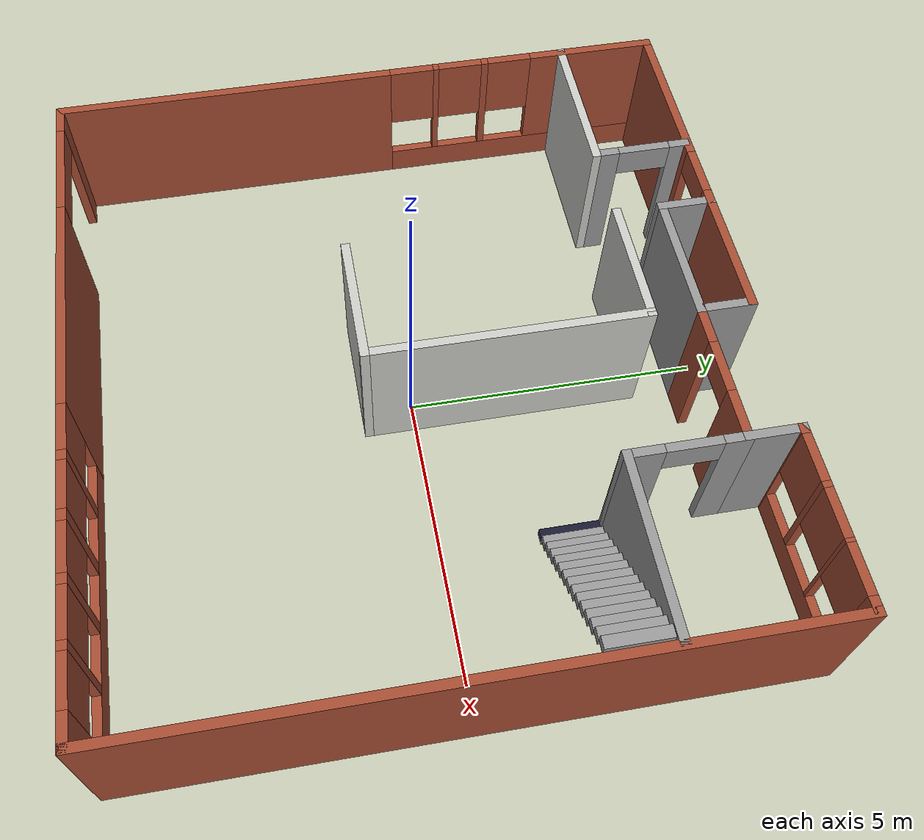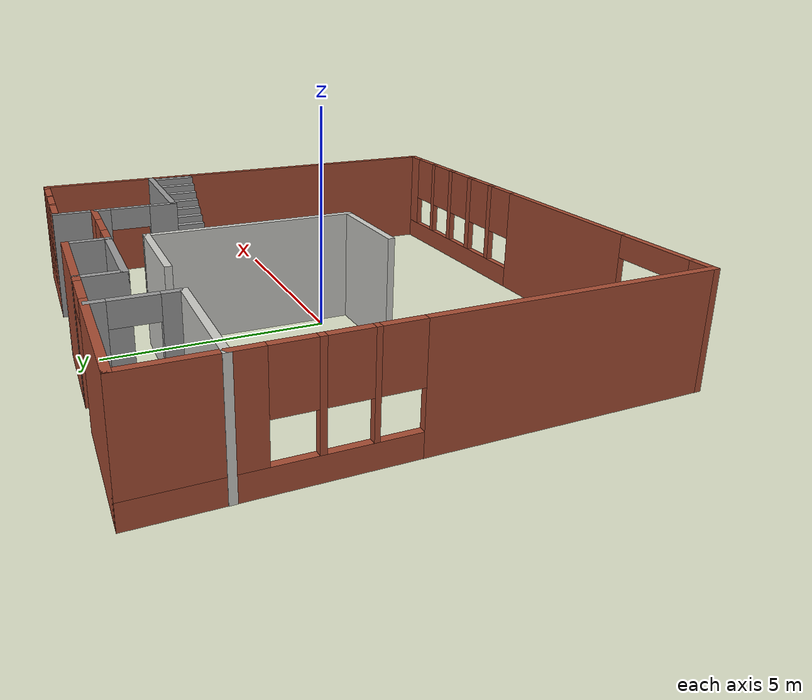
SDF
<?xml version='1.0'?>
<sdf version='1.6'>
  <model name='project1_building'>
    <link name='Stairs_7'>
      <pose frame=''>0 0 0 0 -0 0</pose>
      <self_collide>0</self_collide>
      <kinematic>0</kinematic>
      <gravity>1</gravity>
      <inertial>
        <mass>1</mass>
        <pose frame=''>0 0 0 0 -0 0</pose>
        <inertia>
          <ixx>1</ixx>
          <ixy>0</ixy>
          <ixz>0</ixz>
          <iyy>1</iyy>
          <iyz>0</iyz>
          <izz>1</izz>
        </inertia>
      </inertial>
      <visual name='Stairs_7_Visual_0'>
        <material>
          <ambient>0.1 0.1 0.1 1</ambient>
          <diffuse>0.1 0.1 0.2 1</diffuse>
          <specular>0 0 0 1</specular>
          <emissive>0 0 0 1</emissive>
          <shader type='pixel'>
            <normal_map>__default__</normal_map>
          </shader>
          <script>
            <name>ModelPreview_1::Stairs_7::Stairs_7_Visual_0_MATERIAL_</name>
            <uri>__default__</uri>
          </script>
        </material>
        <pose frame=''>2.81269 2.1369 0.083333 0 -0 1.5708</pose>
        <geometry>
          <box>
            <size>1 0.19 0.166667</size>
          </box>
        </geometry>
        <material>
          <script>
            <uri>file://media/materials/scripts/gazebo.material</uri>
            <name>Gazebo/Grey</name>
          </script>
          <ambient>1 1 1 1</ambient>
        </material>
        <meta>
          <layer>0</layer>
        </meta>
        <transparency>0</transparency>
        <cast_shadows>1</cast_shadows>
      </visual>
      <visual name='Stairs_7_Visual_1'>
        <pose frame=''>3.00269 2.1369 0.25 0 -0 1.5708</pose>
        <geometry>
          <box>
            <size>1 0.19 0.166667</size>
          </box>
        </geometry>
        <material>
          <script>
            <uri>file://media/materials/scripts/gazebo.material</uri>
            <name>Gazebo/Grey</name>
          </script>
          <ambient>1 1 1 1</ambient>
          <shader type='pixel'>
            <normal_map>__default__</normal_map>
          </shader>
          <diffuse>0.7 0.7 0.7 1</diffuse>
          <specular>0.01 0.01 0.01 1</specular>
          <emissive>0 0 0 1</emissive>
        </material>
        <meta>
          <layer>0</layer>
        </meta>
        <transparency>0</transparency>
        <cast_shadows>1</cast_shadows>
      </visual>
      <visual name='Stairs_7_Visual_2'>
        <pose frame=''>3.19269 2.1369 0.416667 0 -0 1.5708</pose>
        <geometry>
          <box>
            <size>1 0.19 0.166667</size>
          </box>
        </geometry>
        <material>
          <script>
            <uri>file://media/materials/scripts/gazebo.material</uri>
            <name>Gazebo/Grey</name>
          </script>
          <ambient>1 1 1 1</ambient>
          <shader type='pixel'>
            <normal_map>__default__</normal_map>
          </shader>
          <diffuse>0.7 0.7 0.7 1</diffuse>
          <specular>0.01 0.01 0.01 1</specular>
          <emissive>0 0 0 1</emissive>
        </material>
        <meta>
          <layer>0</layer>
        </meta>
        <transparency>0</transparency>
        <cast_shadows>1</cast_shadows>
      </visual>
      <visual name='Stairs_7_Visual_3'>
        <pose frame=''>3.38269 2.1369 0.583333 0 -0 1.5708</pose>
        <geometry>
          <box>
            <size>1 0.19 0.166667</size>
          </box>
        </geometry>
        <material>
          <script>
            <uri>file://media/materials/scripts/gazebo.material</uri>
            <name>Gazebo/Grey</name>
          </script>
          <ambient>1 1 1 1</ambient>
          <shader type='pixel'>
            <normal_map>__default__</normal_map>
          </shader>
          <diffuse>0.7 0.7 0.7 1</diffuse>
          <specular>0.01 0.01 0.01 1</specular>
          <emissive>0 0 0 1</emissive>
        </material>
        <meta>
          <layer>0</layer>
        </meta>
        <transparency>0</transparency>
        <cast_shadows>1</cast_shadows>
      </visual>
      <visual name='Stairs_7_Visual_4'>
        <pose frame=''>3.57269 2.1369 0.75 0 -0 1.5708</pose>
        <geometry>
          <box>
            <size>1 0.19 0.166667</size>
          </box>
        </geometry>
        <material>
          <script>
            <uri>file://media/materials/scripts/gazebo.material</uri>
            <name>Gazebo/Grey</name>
          </script>
          <ambient>1 1 1 1</ambient>
          <shader type='pixel'>
            <normal_map>__default__</normal_map>
          </shader>
          <diffuse>0.7 0.7 0.7 1</diffuse>
          <specular>0.01 0.01 0.01 1</specular>
          <emissive>0 0 0 1</emissive>
        </material>
        <meta>
          <layer>0</layer>
        </meta>
        <transparency>0</transparency>
        <cast_shadows>1</cast_shadows>
      </visual>
      <visual name='Stairs_7_Visual_5'>
        <pose frame=''>3.76269 2.1369 0.916667 0 -0 1.5708</pose>
        <geometry>
          <box>
            <size>1 0.19 0.166667</size>
          </box>
        </geometry>
        <material>
          <script>
            <uri>file://media/materials/scripts/gazebo.material</uri>
            <name>Gazebo/Grey</name>
          </script>
          <ambient>1 1 1 1</ambient>
          <shader type='pixel'>
            <normal_map>__default__</normal_map>
          </shader>
          <diffuse>0.7 0.7 0.7 1</diffuse>
          <specular>0.01 0.01 0.01 1</specular>
          <emissive>0 0 0 1</emissive>
        </material>
        <meta>
          <layer>0</layer>
        </meta>
        <transparency>0</transparency>
        <cast_shadows>1</cast_shadows>
      </visual>
      <visual name='Stairs_7_Visual_6'>
        <pose frame=''>3.95269 2.1369 1.08333 0 -0 1.5708</pose>
        <geometry>
          <box>
            <size>1 0.19 0.166667</size>
          </box>
        </geometry>
        <material>
          <script>
            <uri>file://media/materials/scripts/gazebo.material</uri>
            <name>Gazebo/Grey</name>
          </script>
          <ambient>1 1 1 1</ambient>
          <shader type='pixel'>
            <normal_map>__default__</normal_map>
          </shader>
          <diffuse>0.7 0.7 0.7 1</diffuse>
          <specular>0.01 0.01 0.01 1</specular>
          <emissive>0 0 0 1</emissive>
        </material>
        <meta>
          <layer>0</layer>
        </meta>
        <transparency>0</transparency>
        <cast_shadows>1</cast_shadows>
      </visual>
      <visual name='Stairs_7_Visual_7'>
        <pose frame=''>4.14269 2.1369 1.25 0 -0 1.5708</pose>
        <geometry>
          <box>
            <size>1 0.19 0.166667</size>
          </box>
        </geometry>
        <material>
          <script>
            <uri>file://media/materials/scripts/gazebo.material</uri>
            <name>Gazebo/Grey</name>
          </script>
          <ambient>1 1 1 1</ambient>
          <shader type='pixel'>
            <normal_map>__default__</normal_map>
          </shader>
          <diffuse>0.7 0.7 0.7 1</diffuse>
          <specular>0.01 0.01 0.01 1</specular>
          <emissive>0 0 0 1</emissive>
        </material>
        <meta>
          <layer>0</layer>
        </meta>
        <transparency>0</transparency>
        <cast_shadows>1</cast_shadows>
      </visual>
      <visual name='Stairs_7_Visual_8'>
        <pose frame=''>4.33269 2.1369 1.41667 0 -0 1.5708</pose>
        <geometry>
          <box>
            <size>1 0.19 0.166667</size>
          </box>
        </geometry>
        <material>
          <script>
            <uri>file://media/materials/scripts/gazebo.material</uri>
            <name>Gazebo/Grey</name>
          </script>
          <ambient>1 1 1 1</ambient>
          <shader type='pixel'>
            <normal_map>__default__</normal_map>
          </shader>
          <diffuse>0.7 0.7 0.7 1</diffuse>
          <specular>0.01 0.01 0.01 1</specular>
          <emissive>0 0 0 1</emissive>
        </material>
        <meta>
          <layer>0</layer>
        </meta>
        <transparency>0</transparency>
        <cast_shadows>1</cast_shadows>
      </visual>
      <visual name='Stairs_7_Visual_9'>
        <pose frame=''>4.52269 2.1369 1.58333 0 -0 1.5708</pose>
        <geometry>
          <box>
            <size>1 0.19 0.166667</size>
          </box>
        </geometry>
        <material>
          <script>
            <uri>file://media/materials/scripts/gazebo.material</uri>
            <name>Gazebo/Grey</name>
          </script>
          <ambient>1 1 1 1</ambient>
          <shader type='pixel'>
            <normal_map>__default__</normal_map>
          </shader>
          <diffuse>0.7 0.7 0.7 1</diffuse>
          <specular>0.01 0.01 0.01 1</specular>
          <emissive>0 0 0 1</emissive>
        </material>
        <meta>
          <layer>0</layer>
        </meta>
        <transparency>0</transparency>
        <cast_shadows>1</cast_shadows>
      </visual>
      <visual name='Stairs_7_Visual_10'>
        <pose frame=''>4.71269 2.1369 1.75 0 -0 1.5708</pose>
        <geometry>
          <box>
            <size>1 0.19 0.166667</size>
          </box>
        </geometry>
        <material>
          <script>
            <uri>file://media/materials/scripts/gazebo.material</uri>
            <name>Gazebo/Grey</name>
          </script>
          <ambient>1 1 1 1</ambient>
          <shader type='pixel'>
            <normal_map>__default__</normal_map>
          </shader>
          <diffuse>0.7 0.7 0.7 1</diffuse>
          <specular>0.01 0.01 0.01 1</specular>
          <emissive>0 0 0 1</emissive>
        </material>
        <meta>
          <layer>0</layer>
        </meta>
        <transparency>0</transparency>
        <cast_shadows>1</cast_shadows>
      </visual>
      <visual name='Stairs_7_Visual_11'>
        <pose frame=''>4.90269 2.1369 1.91667 0 -0 1.5708</pose>
        <geometry>
          <box>
            <size>1 0.19 0.166667</size>
          </box>
        </geometry>
        <material>
          <script>
            <uri>file://media/materials/scripts/gazebo.material</uri>
            <name>Gazebo/Grey</name>
          </script>
          <ambient>1 1 1 1</ambient>
          <shader type='pixel'>
            <normal_map>__default__</normal_map>
          </shader>
          <diffuse>0.7 0.7 0.7 1</diffuse>
          <specular>0.01 0.01 0.01 1</specular>
          <emissive>0 0 0 1</emissive>
        </material>
        <meta>
          <layer>0</layer>
        </meta>
        <transparency>0</transparency>
        <cast_shadows>1</cast_shadows>
      </visual>
      <visual name='Stairs_7_Visual_12'>
        <pose frame=''>5.09269 2.1369 2.08333 0 -0 1.5708</pose>
        <geometry>
          <box>
            <size>1 0.19 0.166667</size>
          </box>
        </geometry>
        <material>
          <script>
            <uri>file://media/materials/scripts/gazebo.material</uri>
            <name>Gazebo/Grey</name>
          </script>
          <ambient>1 1 1 1</ambient>
          <shader type='pixel'>
            <normal_map>__default__</normal_map>
          </shader>
          <diffuse>0.7 0.7 0.7 1</diffuse>
          <specular>0.01 0.01 0.01 1</specular>
          <emissive>0 0 0 1</emissive>
        </material>
        <meta>
          <layer>0</layer>
        </meta>
        <transparency>0</transparency>
        <cast_shadows>1</cast_shadows>
      </visual>
      <visual name='Stairs_7_Visual_13'>
        <pose frame=''>5.28269 2.1369 2.25 0 -0 1.5708</pose>
        <geometry>
          <box>
            <size>1 0.19 0.166667</size>
          </box>
        </geometry>
        <material>
          <script>
            <uri>file://media/materials/scripts/gazebo.material</uri>
            <name>Gazebo/Grey</name>
          </script>
          <ambient>1 1 1 1</ambient>
          <shader type='pixel'>
            <normal_map>__default__</normal_map>
          </shader>
          <diffuse>0.7 0.7 0.7 1</diffuse>
          <specular>0.01 0.01 0.01 1</specular>
          <emissive>0 0 0 1</emissive>
        </material>
        <meta>
          <layer>0</layer>
        </meta>
        <transparency>0</transparency>
        <cast_shadows>1</cast_shadows>
      </visual>
      <visual name='Stairs_7_Visual_14'>
        <pose frame=''>5.47269 2.1369 2.41667 0 -0 1.5708</pose>
        <geometry>
          <box>
            <size>1 0.19 0.166667</size>
          </box>
        </geometry>
        <material>
          <script>
            <uri>file://media/materials/scripts/gazebo.material</uri>
            <name>Gazebo/Grey</name>
          </script>
          <ambient>1 1 1 1</ambient>
          <shader type='pixel'>
            <normal_map>__default__</normal_map>
          </shader>
          <diffuse>0.7 0.7 0.7 1</diffuse>
          <specular>0.01 0.01 0.01 1</specular>
          <emissive>0 0 0 1</emissive>
        </material>
        <meta>
          <layer>0</layer>
        </meta>
        <transparency>0</transparency>
        <cast_shadows>1</cast_shadows>
      </visual>
      <collision name='Stairs_7_Collision_0'>
        <laser_retro>0</laser_retro>
        <max_contacts>10</max_contacts>
        <pose frame=''>2.81269 2.1369 0.083333 0 -0 1.5708</pose>
        <geometry>
          <box>
            <size>1 0.19 0.166667</size>
          </box>
        </geometry>
        <surface>
          <friction>
            <ode>
              <mu>1</mu>
              <mu2>1</mu2>
              <fdir1>0 0 0</fdir1>
              <slip1>0</slip1>
              <slip2>0</slip2>
            </ode>
            <torsional>
              <coefficient>1</coefficient>
              <patch_radius>0</patch_radius>
              <surface_radius>0</surface_radius>
              <use_patch_radius>1</use_patch_radius>
              <ode>
                <slip>0</slip>
              </ode>
            </torsional>
          </friction>
          <bounce>
            <restitution_coefficient>0</restitution_coefficient>
            <threshold>1e+06</threshold>
          </bounce>
          <contact>
            <collide_without_contact>0</collide_without_contact>
            <collide_without_contact_bitmask>1</collide_without_contact_bitmask>
            <collide_bitmask>1</collide_bitmask>
            <ode>
              <soft_cfm>0</soft_cfm>
              <soft_erp>0.2</soft_erp>
              <kp>1e+13</kp>
              <kd>1</kd>
              <max_vel>0.01</max_vel>
              <min_depth>0</min_depth>
            </ode>
            <bullet>
              <split_impulse>1</split_impulse>
              <split_impulse_penetration_threshold>-0.01</split_impulse_penetration_threshold>
              <soft_cfm>0</soft_cfm>
              <soft_erp>0.2</soft_erp>
              <kp>1e+13</kp>
              <kd>1</kd>
            </bullet>
          </contact>
        </surface>
      </collision>
      <collision name='Stairs_7_Collision_1'>
        <laser_retro>0</laser_retro>
        <max_contacts>10</max_contacts>
        <pose frame=''>3.00269 2.1369 0.25 0 -0 1.5708</pose>
        <geometry>
          <box>
            <size>1 0.19 0.166667</size>
          </box>
        </geometry>
        <surface>
          <friction>
            <ode>
              <mu>1</mu>
              <mu2>1</mu2>
              <fdir1>0 0 0</fdir1>
              <slip1>0</slip1>
              <slip2>0</slip2>
            </ode>
            <torsional>
              <coefficient>1</coefficient>
              <patch_radius>0</patch_radius>
              <surface_radius>0</surface_radius>
              <use_patch_radius>1</use_patch_radius>
              <ode>
                <slip>0</slip>
              </ode>
            </torsional>
          </friction>
          <bounce>
            <restitution_coefficient>0</restitution_coefficient>
            <threshold>1e+06</threshold>
          </bounce>
          <contact>
            <collide_without_contact>0</collide_without_contact>
            <collide_without_contact_bitmask>1</collide_without_contact_bitmask>
            <collide_bitmask>1</collide_bitmask>
            <ode>
              <soft_cfm>0</soft_cfm>
              <soft_erp>0.2</soft_erp>
              <kp>1e+13</kp>
              <kd>1</kd>
              <max_vel>0.01</max_vel>
              <min_depth>0</min_depth>
            </ode>
            <bullet>
              <split_impulse>1</split_impulse>
              <split_impulse_penetration_threshold>-0.01</split_impulse_penetration_threshold>
              <soft_cfm>0</soft_cfm>
              <soft_erp>0.2</soft_erp>
              <kp>1e+13</kp>
              <kd>1</kd>
            </bullet>
          </contact>
        </surface>
      </collision>
      <collision name='Stairs_7_Collision_2'>
        <laser_retro>0</laser_retro>
        <max_contacts>10</max_contacts>
        <pose frame=''>3.19269 2.1369 0.416667 0 -0 1.5708</pose>
        <geometry>
          <box>
            <size>1 0.19 0.166667</size>
          </box>
        </geometry>
        <surface>
          <friction>
            <ode>
              <mu>1</mu>
              <mu2>1</mu2>
              <fdir1>0 0 0</fdir1>
              <slip1>0</slip1>
              <slip2>0</slip2>
            </ode>
            <torsional>
              <coefficient>1</coefficient>
              <patch_radius>0</patch_radius>
              <surface_radius>0</surface_radius>
              <use_patch_radius>1</use_patch_radius>
              <ode>
                <slip>0</slip>
              </ode>
            </torsional>
          </friction>
          <bounce>
            <restitution_coefficient>0</restitution_coefficient>
            <threshold>1e+06</threshold>
          </bounce>
          <contact>
            <collide_without_contact>0</collide_without_contact>
            <collide_without_contact_bitmask>1</collide_without_contact_bitmask>
            <collide_bitmask>1</collide_bitmask>
            <ode>
              <soft_cfm>0</soft_cfm>
              <soft_erp>0.2</soft_erp>
              <kp>1e+13</kp>
              <kd>1</kd>
              <max_vel>0.01</max_vel>
              <min_depth>0</min_depth>
            </ode>
            <bullet>
              <split_impulse>1</split_impulse>
              <split_impulse_penetration_threshold>-0.01</split_impulse_penetration_threshold>
              <soft_cfm>0</soft_cfm>
              <soft_erp>0.2</soft_erp>
              <kp>1e+13</kp>
              <kd>1</kd>
            </bullet>
          </contact>
        </surface>
      </collision>
      <collision name='Stairs_7_Collision_3'>
        <laser_retro>0</laser_retro>
        <max_contacts>10</max_contacts>
        <pose frame=''>3.38269 2.1369 0.583333 0 -0 1.5708</pose>
        <geometry>
          <box>
            <size>1 0.19 0.166667</size>
          </box>
        </geometry>
        <surface>
          <friction>
            <ode>
              <mu>1</mu>
              <mu2>1</mu2>
              <fdir1>0 0 0</fdir1>
              <slip1>0</slip1>
              <slip2>0</slip2>
            </ode>
            <torsional>
              <coefficient>1</coefficient>
              <patch_radius>0</patch_radius>
              <surface_radius>0</surface_radius>
              <use_patch_radius>1</use_patch_radius>
              <ode>
                <slip>0</slip>
              </ode>
            </torsional>
          </friction>
          <bounce>
            <restitution_coefficient>0</restitution_coefficient>
            <threshold>1e+06</threshold>
          </bounce>
          <contact>
            <collide_without_contact>0</collide_without_contact>
            <collide_without_contact_bitmask>1</collide_without_contact_bitmask>
            <collide_bitmask>1</collide_bitmask>
            <ode>
              <soft_cfm>0</soft_cfm>
              <soft_erp>0.2</soft_erp>
              <kp>1e+13</kp>
              <kd>1</kd>
              <max_vel>0.01</max_vel>
              <min_depth>0</min_depth>
            </ode>
            <bullet>
              <split_impulse>1</split_impulse>
              <split_impulse_penetration_threshold>-0.01</split_impulse_penetration_threshold>
              <soft_cfm>0</soft_cfm>
              <soft_erp>0.2</soft_erp>
              <kp>1e+13</kp>
              <kd>1</kd>
            </bullet>
          </contact>
        </surface>
      </collision>
      <collision name='Stairs_7_Collision_4'>
        <laser_retro>0</laser_retro>
        <max_contacts>10</max_contacts>
        <pose frame=''>3.57269 2.1369 0.75 0 -0 1.5708</pose>
        <geometry>
          <box>
            <size>1 0.19 0.166667</size>
          </box>
        </geometry>
        <surface>
          <friction>
            <ode>
              <mu>1</mu>
              <mu2>1</mu2>
              <fdir1>0 0 0</fdir1>
              <slip1>0</slip1>
              <slip2>0</slip2>
            </ode>
            <torsional>
              <coefficient>1</coefficient>
              <patch_radius>0</patch_radius>
              <surface_radius>0</surface_radius>
              <use_patch_radius>1</use_patch_radius>
              <ode>
                <slip>0</slip>
              </ode>
            </torsional>
          </friction>
          <bounce>
            <restitution_coefficient>0</restitution_coefficient>
            <threshold>1e+06</threshold>
          </bounce>
          <contact>
            <collide_without_contact>0</collide_without_contact>
            <collide_without_contact_bitmask>1</collide_without_contact_bitmask>
            <collide_bitmask>1</collide_bitmask>
            <ode>
              <soft_cfm>0</soft_cfm>
              <soft_erp>0.2</soft_erp>
              <kp>1e+13</kp>
              <kd>1</kd>
              <max_vel>0.01</max_vel>
              <min_depth>0</min_depth>
            </ode>
            <bullet>
              <split_impulse>1</split_impulse>
              <split_impulse_penetration_threshold>-0.01</split_impulse_penetration_threshold>
              <soft_cfm>0</soft_cfm>
              <soft_erp>0.2</soft_erp>
              <kp>1e+13</kp>
              <kd>1</kd>
            </bullet>
          </contact>
        </surface>
      </collision>
      <collision name='Stairs_7_Collision_5'>
        <laser_retro>0</laser_retro>
        <max_contacts>10</max_contacts>
        <pose frame=''>3.76269 2.1369 0.916667 0 -0 1.5708</pose>
        <geometry>
          <box>
            <size>1 0.19 0.166667</size>
          </box>
        </geometry>
        <surface>
          <friction>
            <ode>
              <mu>1</mu>
              <mu2>1</mu2>
              <fdir1>0 0 0</fdir1>
              <slip1>0</slip1>
              <slip2>0</slip2>
            </ode>
            <torsional>
              <coefficient>1</coefficient>
              <patch_radius>0</patch_radius>
              <surface_radius>0</surface_radius>
              <use_patch_radius>1</use_patch_radius>
              <ode>
                <slip>0</slip>
              </ode>
            </torsional>
          </friction>
          <bounce>
            <restitution_coefficient>0</restitution_coefficient>
            <threshold>1e+06</threshold>
          </bounce>
          <contact>
            <collide_without_contact>0</collide_without_contact>
            <collide_without_contact_bitmask>1</collide_without_contact_bitmask>
            <collide_bitmask>1</collide_bitmask>
            <ode>
              <soft_cfm>0</soft_cfm>
              <soft_erp>0.2</soft_erp>
              <kp>1e+13</kp>
              <kd>1</kd>
              <max_vel>0.01</max_vel>
              <min_depth>0</min_depth>
            </ode>
            <bullet>
              <split_impulse>1</split_impulse>
              <split_impulse_penetration_threshold>-0.01</split_impulse_penetration_threshold>
              <soft_cfm>0</soft_cfm>
              <soft_erp>0.2</soft_erp>
              <kp>1e+13</kp>
              <kd>1</kd>
            </bullet>
          </contact>
        </surface>
      </collision>
      <collision name='Stairs_7_Collision_6'>
        <laser_retro>0</laser_retro>
        <max_contacts>10</max_contacts>
        <pose frame=''>3.95269 2.1369 1.08333 0 -0 1.5708</pose>
        <geometry>
          <box>
            <size>1 0.19 0.166667</size>
          </box>
        </geometry>
        <surface>
          <friction>
            <ode>
              <mu>1</mu>
              <mu2>1</mu2>
              <fdir1>0 0 0</fdir1>
              <slip1>0</slip1>
              <slip2>0</slip2>
            </ode>
            <torsional>
              <coefficient>1</coefficient>
              <patch_radius>0</patch_radius>
              <surface_radius>0</surface_radius>
              <use_patch_radius>1</use_patch_radius>
              <ode>
                <slip>0</slip>
              </ode>
            </torsional>
          </friction>
          <bounce>
            <restitution_coefficient>0</restitution_coefficient>
            <threshold>1e+06</threshold>
          </bounce>
          <contact>
            <collide_without_contact>0</collide_without_contact>
            <collide_without_contact_bitmask>1</collide_without_contact_bitmask>
            <collide_bitmask>1</collide_bitmask>
            <ode>
              <soft_cfm>0</soft_cfm>
              <soft_erp>0.2</soft_erp>
              <kp>1e+13</kp>
              <kd>1</kd>
              <max_vel>0.01</max_vel>
              <min_depth>0</min_depth>
            </ode>
            <bullet>
              <split_impulse>1</split_impulse>
              <split_impulse_penetration_threshold>-0.01</split_impulse_penetration_threshold>
              <soft_cfm>0</soft_cfm>
              <soft_erp>0.2</soft_erp>
              <kp>1e+13</kp>
              <kd>1</kd>
            </bullet>
          </contact>
        </surface>
      </collision>
      <collision name='Stairs_7_Collision_7'>
        <laser_retro>0</laser_retro>
        <max_contacts>10</max_contacts>
        <pose frame=''>4.14269 2.1369 1.25 0 -0 1.5708</pose>
        <geometry>
          <box>
            <size>1 0.19 0.166667</size>
          </box>
        </geometry>
        <surface>
          <friction>
            <ode>
              <mu>1</mu>
              <mu2>1</mu2>
              <fdir1>0 0 0</fdir1>
              <slip1>0</slip1>
              <slip2>0</slip2>
            </ode>
            <torsional>
              <coefficient>1</coefficient>
              <patch_radius>0</patch_radius>
              <surface_radius>0</surface_radius>
              <use_patch_radius>1</use_patch_radius>
              <ode>
                <slip>0</slip>
              </ode>
            </torsional>
          </friction>
          <bounce>
            <restitution_coefficient>0</restitution_coefficient>
            <threshold>1e+06</threshold>
          </bounce>
          <contact>
            <collide_without_contact>0</collide_without_contact>
            <collide_without_contact_bitmask>1</collide_without_contact_bitmask>
            <collide_bitmask>1</collide_bitmask>
            <ode>
              <soft_cfm>0</soft_cfm>
              <soft_erp>0.2</soft_erp>
              <kp>1e+13</kp>
              <kd>1</kd>
              <max_vel>0.01</max_vel>
              <min_depth>0</min_depth>
            </ode>
            <bullet>
              <split_impulse>1</split_impulse>
              <split_impulse_penetration_threshold>-0.01</split_impulse_penetration_threshold>
              <soft_cfm>0</soft_cfm>
              <soft_erp>0.2</soft_erp>
              <kp>1e+13</kp>
              <kd>1</kd>
            </bullet>
          </contact>
        </surface>
      </collision>
      <collision name='Stairs_7_Collision_8'>
        <laser_retro>0</laser_retro>
        <max_contacts>10</max_contacts>
        <pose frame=''>4.33269 2.1369 1.41667 0 -0 1.5708</pose>
        <geometry>
          <box>
            <size>1 0.19 0.166667</size>
          </box>
        </geometry>
        <surface>
          <friction>
            <ode>
              <mu>1</mu>
              <mu2>1</mu2>
              <fdir1>0 0 0</fdir1>
              <slip1>0</slip1>
              <slip2>0</slip2>
            </ode>
            <torsional>
              <coefficient>1</coefficient>
              <patch_radius>0</patch_radius>
              <surface_radius>0</surface_radius>
              <use_patch_radius>1</use_patch_radius>
              <ode>
                <slip>0</slip>
              </ode>
            </torsional>
          </friction>
          <bounce>
            <restitution_coefficient>0</restitution_coefficient>
            <threshold>1e+06</threshold>
          </bounce>
          <contact>
            <collide_without_contact>0</collide_without_contact>
            <collide_without_contact_bitmask>1</collide_without_contact_bitmask>
            <collide_bitmask>1</collide_bitmask>
            <ode>
              <soft_cfm>0</soft_cfm>
              <soft_erp>0.2</soft_erp>
              <kp>1e+13</kp>
              <kd>1</kd>
              <max_vel>0.01</max_vel>
              <min_depth>0</min_depth>
            </ode>
            <bullet>
              <split_impulse>1</split_impulse>
              <split_impulse_penetration_threshold>-0.01</split_impulse_penetration_threshold>
              <soft_cfm>0</soft_cfm>
              <soft_erp>0.2</soft_erp>
              <kp>1e+13</kp>
              <kd>1</kd>
            </bullet>
          </contact>
        </surface>
      </collision>
      <collision name='Stairs_7_Collision_9'>
        <laser_retro>0</laser_retro>
        <max_contacts>10</max_contacts>
        <pose frame=''>4.52269 2.1369 1.58333 0 -0 1.5708</pose>
        <geometry>
          <box>
            <size>1 0.19 0.166667</size>
          </box>
        </geometry>
        <surface>
          <friction>
            <ode>
              <mu>1</mu>
              <mu2>1</mu2>
              <fdir1>0 0 0</fdir1>
              <slip1>0</slip1>
              <slip2>0</slip2>
            </ode>
            <torsional>
              <coefficient>1</coefficient>
              <patch_radius>0</patch_radius>
              <surface_radius>0</surface_radius>
              <use_patch_radius>1</use_patch_radius>
              <ode>
                <slip>0</slip>
              </ode>
            </torsional>
          </friction>
          <bounce>
            <restitution_coefficient>0</restitution_coefficient>
            <threshold>1e+06</threshold>
          </bounce>
          <contact>
            <collide_without_contact>0</collide_without_contact>
            <collide_without_contact_bitmask>1</collide_without_contact_bitmask>
            <collide_bitmask>1</collide_bitmask>
            <ode>
              <soft_cfm>0</soft_cfm>
              <soft_erp>0.2</soft_erp>
              <kp>1e+13</kp>
              <kd>1</kd>
              <max_vel>0.01</max_vel>
              <min_depth>0</min_depth>
            </ode>
            <bullet>
              <split_impulse>1</split_impulse>
              <split_impulse_penetration_threshold>-0.01</split_impulse_penetration_threshold>
              <soft_cfm>0</soft_cfm>
              <soft_erp>0.2</soft_erp>
              <kp>1e+13</kp>
              <kd>1</kd>
            </bullet>
          </contact>
        </surface>
      </collision>
      <collision name='Stairs_7_Collision_10'>
        <laser_retro>0</laser_retro>
        <max_contacts>10</max_contacts>
        <pose frame=''>4.71269 2.1369 1.75 0 -0 1.5708</pose>
        <geometry>
          <box>
            <size>1 0.19 0.166667</size>
          </box>
        </geometry>
        <surface>
          <friction>
            <ode>
              <mu>1</mu>
              <mu2>1</mu2>
              <fdir1>0 0 0</fdir1>
              <slip1>0</slip1>
              <slip2>0</slip2>
            </ode>
            <torsional>
              <coefficient>1</coefficient>
              <patch_radius>0</patch_radius>
              <surface_radius>0</surface_radius>
              <use_patch_radius>1</use_patch_radius>
              <ode>
                <slip>0</slip>
              </ode>
            </torsional>
          </friction>
          <bounce>
            <restitution_coefficient>0</restitution_coefficient>
            <threshold>1e+06</threshold>
          </bounce>
          <contact>
            <collide_without_contact>0</collide_without_contact>
            <collide_without_contact_bitmask>1</collide_without_contact_bitmask>
            <collide_bitmask>1</collide_bitmask>
            <ode>
              <soft_cfm>0</soft_cfm>
              <soft_erp>0.2</soft_erp>
              <kp>1e+13</kp>
              <kd>1</kd>
              <max_vel>0.01</max_vel>
              <min_depth>0</min_depth>
            </ode>
            <bullet>
              <split_impulse>1</split_impulse>
              <split_impulse_penetration_threshold>-0.01</split_impulse_penetration_threshold>
              <soft_cfm>0</soft_cfm>
              <soft_erp>0.2</soft_erp>
              <kp>1e+13</kp>
              <kd>1</kd>
            </bullet>
          </contact>
        </surface>
      </collision>
      <collision name='Stairs_7_Collision_11'>
        <laser_retro>0</laser_retro>
        <max_contacts>10</max_contacts>
        <pose frame=''>4.90269 2.1369 1.91667 0 -0 1.5708</pose>
        <geometry>
          <box>
            <size>1 0.19 0.166667</size>
          </box>
        </geometry>
        <surface>
          <friction>
            <ode>
              <mu>1</mu>
              <mu2>1</mu2>
              <fdir1>0 0 0</fdir1>
              <slip1>0</slip1>
              <slip2>0</slip2>
            </ode>
            <torsional>
              <coefficient>1</coefficient>
              <patch_radius>0</patch_radius>
              <surface_radius>0</surface_radius>
              <use_patch_radius>1</use_patch_radius>
              <ode>
                <slip>0</slip>
              </ode>
            </torsional>
          </friction>
          <bounce>
            <restitution_coefficient>0</restitution_coefficient>
            <threshold>1e+06</threshold>
          </bounce>
          <contact>
            <collide_without_contact>0</collide_without_contact>
            <collide_without_contact_bitmask>1</collide_without_contact_bitmask>
            <collide_bitmask>1</collide_bitmask>
            <ode>
              <soft_cfm>0</soft_cfm>
              <soft_erp>0.2</soft_erp>
              <kp>1e+13</kp>
              <kd>1</kd>
              <max_vel>0.01</max_vel>
              <min_depth>0</min_depth>
            </ode>
            <bullet>
              <split_impulse>1</split_impulse>
              <split_impulse_penetration_threshold>-0.01</split_impulse_penetration_threshold>
              <soft_cfm>0</soft_cfm>
              <soft_erp>0.2</soft_erp>
              <kp>1e+13</kp>
              <kd>1</kd>
            </bullet>
          </contact>
        </surface>
      </collision>
      <collision name='Stairs_7_Collision_13'>
        <laser_retro>0</laser_retro>
        <max_contacts>10</max_contacts>
        <pose frame=''>5.28269 2.1369 2.25 0 -0 1.5708</pose>
        <geometry>
          <box>
            <size>1 0.19 0.166667</size>
          </box>
        </geometry>
        <surface>
          <friction>
            <ode>
              <mu>1</mu>
              <mu2>1</mu2>
              <fdir1>0 0 0</fdir1>
              <slip1>0</slip1>
              <slip2>0</slip2>
            </ode>
            <torsional>
              <coefficient>1</coefficient>
              <patch_radius>0</patch_radius>
              <surface_radius>0</surface_radius>
              <use_patch_radius>1</use_patch_radius>
              <ode>
                <slip>0</slip>
              </ode>
            </torsional>
          </friction>
          <bounce>
            <restitution_coefficient>0</restitution_coefficient>
            <threshold>1e+06</threshold>
          </bounce>
          <contact>
            <collide_without_contact>0</collide_without_contact>
            <collide_without_contact_bitmask>1</collide_without_contact_bitmask>
            <collide_bitmask>1</collide_bitmask>
            <ode>
              <soft_cfm>0</soft_cfm>
              <soft_erp>0.2</soft_erp>
              <kp>1e+13</kp>
              <kd>1</kd>
              <max_vel>0.01</max_vel>
              <min_depth>0</min_depth>
            </ode>
            <bullet>
              <split_impulse>1</split_impulse>
              <split_impulse_penetration_threshold>-0.01</split_impulse_penetration_threshold>
              <soft_cfm>0</soft_cfm>
              <soft_erp>0.2</soft_erp>
              <kp>1e+13</kp>
              <kd>1</kd>
            </bullet>
          </contact>
        </surface>
      </collision>
      <collision name='Stairs_7_Collision_12'>
        <laser_retro>0</laser_retro>
        <max_contacts>10</max_contacts>
        <pose frame=''>5.09269 2.1369 2.08333 0 -0 1.5708</pose>
        <geometry>
          <box>
            <size>1 0.19 0.166667</size>
          </box>
        </geometry>
        <surface>
          <friction>
            <ode>
              <mu>1</mu>
              <mu2>1</mu2>
              <fdir1>0 0 0</fdir1>
              <slip1>0</slip1>
              <slip2>0</slip2>
            </ode>
            <torsional>
              <coefficient>1</coefficient>
              <patch_radius>0</patch_radius>
              <surface_radius>0</surface_radius>
              <use_patch_radius>1</use_patch_radius>
              <ode>
                <slip>0</slip>
              </ode>
            </torsional>
          </friction>
          <bounce>
            <restitution_coefficient>0</restitution_coefficient>
            <threshold>1e+06</threshold>
          </bounce>
          <contact>
            <collide_without_contact>0</collide_without_contact>
            <collide_without_contact_bitmask>1</collide_without_contact_bitmask>
            <collide_bitmask>1</collide_bitmask>
            <ode>
              <soft_cfm>0</soft_cfm>
              <soft_erp>0.2</soft_erp>
              <kp>1e+13</kp>
              <kd>1</kd>
              <max_vel>0.01</max_vel>
              <min_depth>0</min_depth>
            </ode>
            <bullet>
              <split_impulse>1</split_impulse>
              <split_impulse_penetration_threshold>-0.01</split_impulse_penetration_threshold>
              <soft_cfm>0</soft_cfm>
              <soft_erp>0.2</soft_erp>
              <kp>1e+13</kp>
              <kd>1</kd>
            </bullet>
          </contact>
        </surface>
      </collision>
      <collision name='Stairs_7_Collision_14'>
        <laser_retro>0</laser_retro>
        <max_contacts>10</max_contacts>
        <pose frame=''>5.47269 2.1369 2.41667 0 -0 1.5708</pose>
        <geometry>
          <box>
            <size>1 0.19 0.166667</size>
          </box>
        </geometry>
        <surface>
          <friction>
            <ode>
              <mu>1</mu>
              <mu2>1</mu2>
              <fdir1>0 0 0</fdir1>
              <slip1>0</slip1>
              <slip2>0</slip2>
            </ode>
            <torsional>
              <coefficient>1</coefficient>
              <patch_radius>0</patch_radius>
              <surface_radius>0</surface_radius>
              <use_patch_radius>1</use_patch_radius>
              <ode>
                <slip>0</slip>
              </ode>
            </torsional>
          </friction>
          <bounce>
            <restitution_coefficient>0</restitution_coefficient>
            <threshold>1e+06</threshold>
          </bounce>
          <contact>
            <collide_without_contact>0</collide_without_contact>
            <collide_without_contact_bitmask>1</collide_without_contact_bitmask>
            <collide_bitmask>1</collide_bitmask>
            <ode>
              <soft_cfm>0</soft_cfm>
              <soft_erp>0.2</soft_erp>
              <kp>1e+13</kp>
              <kd>1</kd>
              <max_vel>0.01</max_vel>
              <min_depth>0</min_depth>
            </ode>
            <bullet>
              <split_impulse>1</split_impulse>
              <split_impulse_penetration_threshold>-0.01</split_impulse_penetration_threshold>
              <soft_cfm>0</soft_cfm>
              <soft_erp>0.2</soft_erp>
              <kp>1e+13</kp>
              <kd>1</kd>
            </bullet>
          </contact>
        </surface>
      </collision>
    </link>
    <link name='Wall_0'>
      <pose frame=''>-5.67233 0 0 0 -0 1.5708</pose>
      <self_collide>0</self_collide>
      <kinematic>0</kinematic>
      <visual name='Wall_0_Visual_0'>
        <pose frame=''>-2.47085 0 1.25 0 -0 0</pose>
        <geometry>
          <box>
            <size>6.0583 0.15 2.5</size>
          </box>
        </geometry>
        <material>
          <script>
            <uri>file://media/materials/scripts/gazebo.material</uri>
            <name>Gazebo/Bricks</name>
          </script>
          <ambient>1 1 1 1</ambient>
          <shader type='pixel'/>
          <diffuse>1 1 1 1</diffuse>
          <specular>0.2 0.2 0.2 1</specular>
          <emissive>0 0 0 1</emissive>
        </material>
        <meta>
          <layer>0</layer>
        </meta>
        <transparency>0</transparency>
        <cast_shadows>1</cast_shadows>
      </visual>
      <visual name='Wall_0_Visual_1'>
        <pose frame=''>3.02915 0 0.25 0 -0 0</pose>
        <geometry>
          <box>
            <size>4.9417 0.15 0.5</size>
          </box>
        </geometry>
        <material>
          <script>
            <uri>file://media/materials/scripts/gazebo.material</uri>
            <name>Gazebo/Bricks</name>
          </script>
          <ambient>1 1 1 1</ambient>
          <shader type='pixel'/>
          <diffuse>1 1 1 1</diffuse>
          <specular>0.2 0.2 0.2 1</specular>
          <emissive>0 0 0 1</emissive>
        </material>
        <meta>
          <layer>0</layer>
        </meta>
        <transparency>0</transparency>
        <cast_shadows>1</cast_shadows>
      </visual>
      <visual name='Wall_0_Visual_2'>
        <pose frame=''>1.41086 0 1.5 0 -0 0</pose>
        <geometry>
          <box>
            <size>0.105111 0.15 2</size>
          </box>
        </geometry>
        <material>
          <script>
            <uri>file://media/materials/scripts/gazebo.material</uri>
            <name>Gazebo/Bricks</name>
          </script>
          <ambient>1 1 1 1</ambient>
          <shader type='pixel'/>
          <diffuse>1 1 1 1</diffuse>
          <specular>0.2 0.2 0.2 1</specular>
          <emissive>0 0 0 1</emissive>
        </material>
        <meta>
          <layer>0</layer>
        </meta>
        <transparency>0</transparency>
        <cast_shadows>1</cast_shadows>
      </visual>
      <visual name='Wall_0_Visual_3'>
        <pose frame=''>2.32602 0 1.5 0 -0 0</pose>
        <geometry>
          <box>
            <size>0.125224 0.15 2</size>
          </box>
        </geometry>
        <material>
          <script>
            <uri>file://media/materials/scripts/gazebo.material</uri>
            <name>Gazebo/Bricks</name>
          </script>
          <ambient>1 1 1 1</ambient>
          <shader type='pixel'/>
          <diffuse>1 1 1 1</diffuse>
          <specular>0.2 0.2 0.2 1</specular>
          <emissive>0 0 0 1</emissive>
        </material>
        <meta>
          <layer>0</layer>
        </meta>
        <transparency>0</transparency>
        <cast_shadows>1</cast_shadows>
      </visual>
      <visual name='Wall_0_Visual_4'>
        <pose frame=''>4.34432 0 1.5 0 -0 0</pose>
        <geometry>
          <box>
            <size>2.31136 0.15 2</size>
          </box>
        </geometry>
        <material>
          <script>
            <uri>file://media/materials/scripts/gazebo.material</uri>
            <name>Gazebo/Bricks</name>
          </script>
          <ambient>1 1 1 1</ambient>
          <shader type='pixel'/>
          <diffuse>1 1 1 1</diffuse>
          <specular>0.2 0.2 0.2 1</specular>
          <emissive>0 0 0 1</emissive>
        </material>
        <meta>
          <layer>0</layer>
        </meta>
        <transparency>0</transparency>
        <cast_shadows>1</cast_shadows>
      </visual>
      <visual name='Wall_0_Visual_5'>
        <pose frame=''>0.9583 0 1.9 0 -0 0</pose>
        <geometry>
          <box>
            <size>0.8 0.15 1.2</size>
          </box>
        </geometry>
        <material>
          <script>
            <uri>file://media/materials/scripts/gazebo.material</uri>
            <name>Gazebo/Bricks</name>
          </script>
          <ambient>1 1 1 1</ambient>
          <shader type='pixel'/>
          <diffuse>1 1 1 1</diffuse>
          <specular>0.2 0.2 0.2 1</specular>
          <emissive>0 0 0 1</emissive>
        </material>
        <meta>
          <layer>0</layer>
        </meta>
        <transparency>0</transparency>
        <cast_shadows>1</cast_shadows>
      </visual>
      <visual name='Wall_0_Visual_6'>
        <pose frame=''>1.86341 0 1.9 0 -0 0</pose>
        <geometry>
          <box>
            <size>0.8 0.15 1.2</size>
          </box>
        </geometry>
        <material>
          <script>
            <uri>file://media/materials/scripts/gazebo.material</uri>
            <name>Gazebo/Bricks</name>
          </script>
          <ambient>1 1 1 1</ambient>
          <shader type='pixel'/>
          <diffuse>1 1 1 1</diffuse>
          <specular>0.2 0.2 0.2 1</specular>
          <emissive>0 0 0 1</emissive>
        </material>
        <meta>
          <layer>0</layer>
        </meta>
        <transparency>0</transparency>
        <cast_shadows>1</cast_shadows>
      </visual>
      <visual name='Wall_0_Visual_7'>
        <pose frame=''>2.78864 0 1.9 0 -0 0</pose>
        <geometry>
          <box>
            <size>0.8 0.15 1.2</size>
          </box>
        </geometry>
        <material>
          <script>
            <uri>file://media/materials/scripts/gazebo.material</uri>
            <name>Gazebo/Bricks</name>
          </script>
          <ambient>1 1 1 1</ambient>
          <shader type='pixel'/>
          <diffuse>1 1 1 1</diffuse>
          <specular>0.2 0.2 0.2 1</specular>
          <emissive>0 0 0 1</emissive>
        </material>
        <meta>
          <layer>0</layer>
        </meta>
        <transparency>0</transparency>
        <cast_shadows>1</cast_shadows>
      </visual>
      <collision name='Wall_0_Collision_1'>
        <laser_retro>0</laser_retro>
        <max_contacts>10</max_contacts>
        <pose frame=''>3.02915 0 0.25 0 -0 0</pose>
        <geometry>
          <box>
            <size>4.9417 0.15 0.5</size>
          </box>
        </geometry>
        <surface>
          <friction>
            <ode>
              <mu>1</mu>
              <mu2>1</mu2>
              <fdir1>0 0 0</fdir1>
              <slip1>0</slip1>
              <slip2>0</slip2>
            </ode>
            <torsional>
              <coefficient>1</coefficient>
              <patch_radius>0</patch_radius>
              <surface_radius>0</surface_radius>
              <use_patch_radius>1</use_patch_radius>
              <ode>
                <slip>0</slip>
              </ode>
            </torsional>
          </friction>
          <bounce>
            <restitution_coefficient>0</restitution_coefficient>
            <threshold>1e+06</threshold>
          </bounce>
          <contact>
            <collide_without_contact>0</collide_without_contact>
            <collide_without_contact_bitmask>1</collide_without_contact_bitmask>
            <collide_bitmask>1</collide_bitmask>
            <ode>
              <soft_cfm>0</soft_cfm>
              <soft_erp>0.2</soft_erp>
              <kp>1e+13</kp>
              <kd>1</kd>
              <max_vel>0.01</max_vel>
              <min_depth>0</min_depth>
            </ode>
            <bullet>
              <split_impulse>1</split_impulse>
              <split_impulse_penetration_threshold>-0.01</split_impulse_penetration_threshold>
              <soft_cfm>0</soft_cfm>
              <soft_erp>0.2</soft_erp>
              <kp>1e+13</kp>
              <kd>1</kd>
            </bullet>
          </contact>
        </surface>
      </collision>
      <collision name='Wall_0_Collision_0'>
        <laser_retro>0</laser_retro>
        <max_contacts>10</max_contacts>
        <pose frame=''>-2.47085 0 1.25 0 -0 0</pose>
        <geometry>
          <box>
            <size>6.0583 0.15 2.5</size>
          </box>
        </geometry>
        <surface>
          <friction>
            <ode>
              <mu>1</mu>
              <mu2>1</mu2>
              <fdir1>0 0 0</fdir1>
              <slip1>0</slip1>
              <slip2>0</slip2>
            </ode>
            <torsional>
              <coefficient>1</coefficient>
              <patch_radius>0</patch_radius>
              <surface_radius>0</surface_radius>
              <use_patch_radius>1</use_patch_radius>
              <ode>
                <slip>0</slip>
              </ode>
            </torsional>
          </friction>
          <bounce>
            <restitution_coefficient>0</restitution_coefficient>
            <threshold>1e+06</threshold>
          </bounce>
          <contact>
            <collide_without_contact>0</collide_without_contact>
            <collide_without_contact_bitmask>1</collide_without_contact_bitmask>
            <collide_bitmask>1</collide_bitmask>
            <ode>
              <soft_cfm>0</soft_cfm>
              <soft_erp>0.2</soft_erp>
              <kp>1e+13</kp>
              <kd>1</kd>
              <max_vel>0.01</max_vel>
              <min_depth>0</min_depth>
            </ode>
            <bullet>
              <split_impulse>1</split_impulse>
              <split_impulse_penetration_threshold>-0.01</split_impulse_penetration_threshold>
              <soft_cfm>0</soft_cfm>
              <soft_erp>0.2</soft_erp>
              <kp>1e+13</kp>
              <kd>1</kd>
            </bullet>
          </contact>
        </surface>
      </collision>
      <collision name='Wall_0_Collision_2'>
        <laser_retro>0</laser_retro>
        <max_contacts>10</max_contacts>
        <pose frame=''>1.41086 0 1.5 0 -0 0</pose>
        <geometry>
          <box>
            <size>0.105111 0.15 2</size>
          </box>
        </geometry>
        <surface>
          <friction>
            <ode>
              <mu>1</mu>
              <mu2>1</mu2>
              <fdir1>0 0 0</fdir1>
              <slip1>0</slip1>
              <slip2>0</slip2>
            </ode>
            <torsional>
              <coefficient>1</coefficient>
              <patch_radius>0</patch_radius>
              <surface_radius>0</surface_radius>
              <use_patch_radius>1</use_patch_radius>
              <ode>
                <slip>0</slip>
              </ode>
            </torsional>
          </friction>
          <bounce>
            <restitution_coefficient>0</restitution_coefficient>
            <threshold>1e+06</threshold>
          </bounce>
          <contact>
            <collide_without_contact>0</collide_without_contact>
            <collide_without_contact_bitmask>1</collide_without_contact_bitmask>
            <collide_bitmask>1</collide_bitmask>
            <ode>
              <soft_cfm>0</soft_cfm>
              <soft_erp>0.2</soft_erp>
              <kp>1e+13</kp>
              <kd>1</kd>
              <max_vel>0.01</max_vel>
              <min_depth>0</min_depth>
            </ode>
            <bullet>
              <split_impulse>1</split_impulse>
              <split_impulse_penetration_threshold>-0.01</split_impulse_penetration_threshold>
              <soft_cfm>0</soft_cfm>
              <soft_erp>0.2</soft_erp>
              <kp>1e+13</kp>
              <kd>1</kd>
            </bullet>
          </contact>
        </surface>
      </collision>
      <collision name='Wall_0_Collision_5'>
        <laser_retro>0</laser_retro>
        <max_contacts>10</max_contacts>
        <pose frame=''>0.9583 0 1.9 0 -0 0</pose>
        <geometry>
          <box>
            <size>0.8 0.15 1.2</size>
          </box>
        </geometry>
        <surface>
          <friction>
            <ode>
              <mu>1</mu>
              <mu2>1</mu2>
              <fdir1>0 0 0</fdir1>
              <slip1>0</slip1>
              <slip2>0</slip2>
            </ode>
            <torsional>
              <coefficient>1</coefficient>
              <patch_radius>0</patch_radius>
              <surface_radius>0</surface_radius>
              <use_patch_radius>1</use_patch_radius>
              <ode>
                <slip>0</slip>
              </ode>
            </torsional>
          </friction>
          <bounce>
            <restitution_coefficient>0</restitution_coefficient>
            <threshold>1e+06</threshold>
          </bounce>
          <contact>
            <collide_without_contact>0</collide_without_contact>
            <collide_without_contact_bitmask>1</collide_without_contact_bitmask>
            <collide_bitmask>1</collide_bitmask>
            <ode>
              <soft_cfm>0</soft_cfm>
              <soft_erp>0.2</soft_erp>
              <kp>1e+13</kp>
              <kd>1</kd>
              <max_vel>0.01</max_vel>
              <min_depth>0</min_depth>
            </ode>
            <bullet>
              <split_impulse>1</split_impulse>
              <split_impulse_penetration_threshold>-0.01</split_impulse_penetration_threshold>
              <soft_cfm>0</soft_cfm>
              <soft_erp>0.2</soft_erp>
              <kp>1e+13</kp>
              <kd>1</kd>
            </bullet>
          </contact>
        </surface>
      </collision>
      <collision name='Wall_0_Collision_3'>
        <laser_retro>0</laser_retro>
        <max_contacts>10</max_contacts>
        <pose frame=''>2.32602 0 1.5 0 -0 0</pose>
        <geometry>
          <box>
            <size>0.125224 0.15 2</size>
          </box>
        </geometry>
        <surface>
          <friction>
            <ode>
              <mu>1</mu>
              <mu2>1</mu2>
              <fdir1>0 0 0</fdir1>
              <slip1>0</slip1>
              <slip2>0</slip2>
            </ode>
            <torsional>
              <coefficient>1</coefficient>
              <patch_radius>0</patch_radius>
              <surface_radius>0</surface_radius>
              <use_patch_radius>1</use_patch_radius>
              <ode>
                <slip>0</slip>
              </ode>
            </torsional>
          </friction>
          <bounce>
            <restitution_coefficient>0</restitution_coefficient>
            <threshold>1e+06</threshold>
          </bounce>
          <contact>
            <collide_without_contact>0</collide_without_contact>
            <collide_without_contact_bitmask>1</collide_without_contact_bitmask>
            <collide_bitmask>1</collide_bitmask>
            <ode>
              <soft_cfm>0</soft_cfm>
              <soft_erp>0.2</soft_erp>
              <kp>1e+13</kp>
              <kd>1</kd>
              <max_vel>0.01</max_vel>
              <min_depth>0</min_depth>
            </ode>
            <bullet>
              <split_impulse>1</split_impulse>
              <split_impulse_penetration_threshold>-0.01</split_impulse_penetration_threshold>
              <soft_cfm>0</soft_cfm>
              <soft_erp>0.2</soft_erp>
              <kp>1e+13</kp>
              <kd>1</kd>
            </bullet>
          </contact>
        </surface>
      </collision>
      <collision name='Wall_0_Collision_4'>
        <laser_retro>0</laser_retro>
        <max_contacts>10</max_contacts>
        <pose frame=''>4.34432 0 1.5 0 -0 0</pose>
        <geometry>
          <box>
            <size>2.31136 0.15 2</size>
          </box>
        </geometry>
        <surface>
          <friction>
            <ode>
              <mu>1</mu>
              <mu2>1</mu2>
              <fdir1>0 0 0</fdir1>
              <slip1>0</slip1>
              <slip2>0</slip2>
            </ode>
            <torsional>
              <coefficient>1</coefficient>
              <patch_radius>0</patch_radius>
              <surface_radius>0</surface_radius>
              <use_patch_radius>1</use_patch_radius>
              <ode>
                <slip>0</slip>
              </ode>
            </torsional>
          </friction>
          <bounce>
            <restitution_coefficient>0</restitution_coefficient>
            <threshold>1e+06</threshold>
          </bounce>
          <contact>
            <collide_without_contact>0</collide_without_contact>
            <collide_without_contact_bitmask>1</collide_without_contact_bitmask>
            <collide_bitmask>1</collide_bitmask>
            <ode>
              <soft_cfm>0</soft_cfm>
              <soft_erp>0.2</soft_erp>
              <kp>1e+13</kp>
              <kd>1</kd>
              <max_vel>0.01</max_vel>
              <min_depth>0</min_depth>
            </ode>
            <bullet>
              <split_impulse>1</split_impulse>
              <split_impulse_penetration_threshold>-0.01</split_impulse_penetration_threshold>
              <soft_cfm>0</soft_cfm>
              <soft_erp>0.2</soft_erp>
              <kp>1e+13</kp>
              <kd>1</kd>
            </bullet>
          </contact>
        </surface>
      </collision>
      <collision name='Wall_0_Collision_6'>
        <laser_retro>0</laser_retro>
        <max_contacts>10</max_contacts>
        <pose frame=''>1.86341 0 1.9 0 -0 0</pose>
        <geometry>
          <box>
            <size>0.8 0.15 1.2</size>
          </box>
        </geometry>
        <surface>
          <friction>
            <ode>
              <mu>1</mu>
              <mu2>1</mu2>
              <fdir1>0 0 0</fdir1>
              <slip1>0</slip1>
              <slip2>0</slip2>
            </ode>
            <torsional>
              <coefficient>1</coefficient>
              <patch_radius>0</patch_radius>
              <surface_radius>0</surface_radius>
              <use_patch_radius>1</use_patch_radius>
              <ode>
                <slip>0</slip>
              </ode>
            </torsional>
          </friction>
          <bounce>
            <restitution_coefficient>0</restitution_coefficient>
            <threshold>1e+06</threshold>
          </bounce>
          <contact>
            <collide_without_contact>0</collide_without_contact>
            <collide_without_contact_bitmask>1</collide_without_contact_bitmask>
            <collide_bitmask>1</collide_bitmask>
            <ode>
              <soft_cfm>0</soft_cfm>
              <soft_erp>0.2</soft_erp>
              <kp>1e+13</kp>
              <kd>1</kd>
              <max_vel>0.01</max_vel>
              <min_depth>0</min_depth>
            </ode>
            <bullet>
              <split_impulse>1</split_impulse>
              <split_impulse_penetration_threshold>-0.01</split_impulse_penetration_threshold>
              <soft_cfm>0</soft_cfm>
              <soft_erp>0.2</soft_erp>
              <kp>1e+13</kp>
              <kd>1</kd>
            </bullet>
          </contact>
        </surface>
      </collision>
      <collision name='Wall_0_Collision_7'>
        <laser_retro>0</laser_retro>
        <max_contacts>10</max_contacts>
        <pose frame=''>2.78864 0 1.9 0 -0 0</pose>
        <geometry>
          <box>
            <size>0.8 0.15 1.2</size>
          </box>
        </geometry>
        <surface>
          <friction>
            <ode>
              <mu>1</mu>
              <mu2>1</mu2>
              <fdir1>0 0 0</fdir1>
              <slip1>0</slip1>
              <slip2>0</slip2>
            </ode>
            <torsional>
              <coefficient>1</coefficient>
              <patch_radius>0</patch_radius>
              <surface_radius>0</surface_radius>
              <use_patch_radius>1</use_patch_radius>
              <ode>
                <slip>0</slip>
              </ode>
            </torsional>
          </friction>
          <bounce>
            <restitution_coefficient>0</restitution_coefficient>
            <threshold>1e+06</threshold>
          </bounce>
          <contact>
            <collide_without_contact>0</collide_without_contact>
            <collide_without_contact_bitmask>1</collide_without_contact_bitmask>
            <collide_bitmask>1</collide_bitmask>
            <ode>
              <soft_cfm>0</soft_cfm>
              <soft_erp>0.2</soft_erp>
              <kp>1e+13</kp>
              <kd>1</kd>
              <max_vel>0.01</max_vel>
              <min_depth>0</min_depth>
            </ode>
            <bullet>
              <split_impulse>1</split_impulse>
              <split_impulse_penetration_threshold>-0.01</split_impulse_penetration_threshold>
              <soft_cfm>0</soft_cfm>
              <soft_erp>0.2</soft_erp>
              <kp>1e+13</kp>
              <kd>1</kd>
            </bullet>
          </contact>
        </surface>
      </collision>
    </link>
    <link name='Wall_1'>
      <pose frame=''>-2.62233 5.425 0 0 -0 0</pose>
      <self_collide>0</self_collide>
      <kinematic>0</kinematic>
      <visual name='Wall_1_Visual_0'>
        <pose frame=''>-1.67324 0 1.25 0 -0 0</pose>
        <geometry>
          <box>
            <size>2.90351 0.15 2.5</size>
          </box>
        </geometry>
        <material>
          <script>
            <uri>file://media/materials/scripts/gazebo.material</uri>
            <name>Gazebo/Bricks</name>
          </script>
          <ambient>1 1 1 1</ambient>
          <shader type='pixel'/>
          <diffuse>1 1 1 1</diffuse>
          <specular>0.2 0.2 0.2 1</specular>
          <emissive>0 0 0 1</emissive>
        </material>
        <meta>
          <layer>0</layer>
        </meta>
        <transparency>0</transparency>
        <cast_shadows>1</cast_shadows>
      </visual>
      <visual name='Wall_1_Visual_1'>
        <pose frame=''>1.90176 0 1.25 0 -0 0</pose>
        <geometry>
          <box>
            <size>2.44649 0.15 2.5</size>
          </box>
        </geometry>
        <material>
          <script>
            <uri>file://media/materials/scripts/gazebo.material</uri>
            <name>Gazebo/Bricks</name>
          </script>
          <ambient>1 1 1 1</ambient>
          <shader type='pixel'/>
          <diffuse>1 1 1 1</diffuse>
          <specular>0.2 0.2 0.2 1</specular>
          <emissive>0 0 0 1</emissive>
        </material>
        <meta>
          <layer>0</layer>
        </meta>
        <transparency>0</transparency>
        <cast_shadows>1</cast_shadows>
      </visual>
      <visual name='Wall_1_Visual_2'>
        <pose frame=''>0.228513 0 2.25 0 -0 0</pose>
        <geometry>
          <box>
            <size>0.9 0.15 0.5</size>
          </box>
        </geometry>
        <material>
          <script>
            <uri>file://media/materials/scripts/gazebo.material</uri>
            <name>Gazebo/Bricks</name>
          </script>
          <ambient>1 1 1 1</ambient>
          <shader type='pixel'/>
          <diffuse>1 1 1 1</diffuse>
          <specular>0.2 0.2 0.2 1</specular>
          <emissive>0 0 0 1</emissive>
        </material>
        <meta>
          <layer>0</layer>
        </meta>
        <transparency>0</transparency>
        <cast_shadows>1</cast_shadows>
      </visual>
      <collision name='Wall_1_Collision_0'>
        <laser_retro>0</laser_retro>
        <max_contacts>10</max_contacts>
        <pose frame=''>-1.67324 0 1.25 0 -0 0</pose>
        <geometry>
          <box>
            <size>2.90351 0.15 2.5</size>
          </box>
        </geometry>
        <surface>
          <friction>
            <ode>
              <mu>1</mu>
              <mu2>1</mu2>
              <fdir1>0 0 0</fdir1>
              <slip1>0</slip1>
              <slip2>0</slip2>
            </ode>
            <torsional>
              <coefficient>1</coefficient>
              <patch_radius>0</patch_radius>
              <surface_radius>0</surface_radius>
              <use_patch_radius>1</use_patch_radius>
              <ode>
                <slip>0</slip>
              </ode>
            </torsional>
          </friction>
          <bounce>
            <restitution_coefficient>0</restitution_coefficient>
            <threshold>1e+06</threshold>
          </bounce>
          <contact>
            <collide_without_contact>0</collide_without_contact>
            <collide_without_contact_bitmask>1</collide_without_contact_bitmask>
            <collide_bitmask>1</collide_bitmask>
            <ode>
              <soft_cfm>0</soft_cfm>
              <soft_erp>0.2</soft_erp>
              <kp>1e+13</kp>
              <kd>1</kd>
              <max_vel>0.01</max_vel>
              <min_depth>0</min_depth>
            </ode>
            <bullet>
              <split_impulse>1</split_impulse>
              <split_impulse_penetration_threshold>-0.01</split_impulse_penetration_threshold>
              <soft_cfm>0</soft_cfm>
              <soft_erp>0.2</soft_erp>
              <kp>1e+13</kp>
              <kd>1</kd>
            </bullet>
          </contact>
        </surface>
      </collision>
      <collision name='Wall_1_Collision_2'>
        <laser_retro>0</laser_retro>
        <max_contacts>10</max_contacts>
        <pose frame=''>0.228513 0 2.25 0 -0 0</pose>
        <geometry>
          <box>
            <size>0.9 0.15 0.5</size>
          </box>
        </geometry>
        <surface>
          <friction>
            <ode>
              <mu>1</mu>
              <mu2>1</mu2>
              <fdir1>0 0 0</fdir1>
              <slip1>0</slip1>
              <slip2>0</slip2>
            </ode>
            <torsional>
              <coefficient>1</coefficient>
              <patch_radius>0</patch_radius>
              <surface_radius>0</surface_radius>
              <use_patch_radius>1</use_patch_radius>
              <ode>
                <slip>0</slip>
              </ode>
            </torsional>
          </friction>
          <bounce>
            <restitution_coefficient>0</restitution_coefficient>
            <threshold>1e+06</threshold>
          </bounce>
          <contact>
            <collide_without_contact>0</collide_without_contact>
            <collide_without_contact_bitmask>1</collide_without_contact_bitmask>
            <collide_bitmask>1</collide_bitmask>
            <ode>
              <soft_cfm>0</soft_cfm>
              <soft_erp>0.2</soft_erp>
              <kp>1e+13</kp>
              <kd>1</kd>
              <max_vel>0.01</max_vel>
              <min_depth>0</min_depth>
            </ode>
            <bullet>
              <split_impulse>1</split_impulse>
              <split_impulse_penetration_threshold>-0.01</split_impulse_penetration_threshold>
              <soft_cfm>0</soft_cfm>
              <soft_erp>0.2</soft_erp>
              <kp>1e+13</kp>
              <kd>1</kd>
            </bullet>
          </contact>
        </surface>
      </collision>
      <collision name='Wall_1_Collision_1'>
        <laser_retro>0</laser_retro>
        <max_contacts>10</max_contacts>
        <pose frame=''>1.90176 0 1.25 0 -0 0</pose>
        <geometry>
          <box>
            <size>2.44649 0.15 2.5</size>
          </box>
        </geometry>
        <surface>
          <friction>
            <ode>
              <mu>1</mu>
              <mu2>1</mu2>
              <fdir1>0 0 0</fdir1>
              <slip1>0</slip1>
              <slip2>0</slip2>
            </ode>
            <torsional>
              <coefficient>1</coefficient>
              <patch_radius>0</patch_radius>
              <surface_radius>0</surface_radius>
              <use_patch_radius>1</use_patch_radius>
              <ode>
                <slip>0</slip>
              </ode>
            </torsional>
          </friction>
          <bounce>
            <restitution_coefficient>0</restitution_coefficient>
            <threshold>1e+06</threshold>
          </bounce>
          <contact>
            <collide_without_contact>0</collide_without_contact>
            <collide_without_contact_bitmask>1</collide_without_contact_bitmask>
            <collide_bitmask>1</collide_bitmask>
            <ode>
              <soft_cfm>0</soft_cfm>
              <soft_erp>0.2</soft_erp>
              <kp>1e+13</kp>
              <kd>1</kd>
              <max_vel>0.01</max_vel>
              <min_depth>0</min_depth>
            </ode>
            <bullet>
              <split_impulse>1</split_impulse>
              <split_impulse_penetration_threshold>-0.01</split_impulse_penetration_threshold>
              <soft_cfm>0</soft_cfm>
              <soft_erp>0.2</soft_erp>
              <kp>1e+13</kp>
              <kd>1</kd>
            </bullet>
          </contact>
        </surface>
      </collision>
    </link>
    <link name='Wall_11'>
      <pose frame=''>5.67767 0 0 0 -0 1.5708</pose>
      <self_collide>0</self_collide>
      <kinematic>0</kinematic>
      <gravity>1</gravity>
      <inertial>
        <mass>1</mass>
        <pose frame=''>0 0 0 0 -0 0</pose>
        <inertia>
          <ixx>1</ixx>
          <ixy>0</ixy>
          <ixz>0</ixz>
          <iyy>1</iyy>
          <iyz>0</iyz>
          <izz>1</izz>
        </inertia>
      </inertial>
      <visual name='Wall_11_Visual'>
        <pose frame=''>0 0 1.25 0 -0 0</pose>
        <geometry>
          <box>
            <size>11 0.15 2.5</size>
          </box>
        </geometry>
        <material>
          <script>
            <uri>file://media/materials/scripts/gazebo.material</uri>
            <name>Gazebo/Bricks</name>
          </script>
          <ambient>1 0 0 0</ambient>
          <shader type='pixel'>
            <normal_map>__default__</normal_map>
          </shader>
          <diffuse>1 0 0 0</diffuse>
          <specular>0 0.2 0.2 1</specular>
          <emissive>0 0 0 1</emissive>
        </material>
        <meta>
          <layer>0</layer>
        </meta>
        <transparency>0</transparency>
        <cast_shadows>1</cast_shadows>
      </visual>
      <collision name='Wall_11_Collision'>
        <laser_retro>0</laser_retro>
        <max_contacts>10</max_contacts>
        <pose frame=''>0 0 1.25 0 -0 0</pose>
        <geometry>
          <box>
            <size>11 0.15 2.5</size>
          </box>
        </geometry>
        <surface>
          <friction>
            <ode>
              <mu>1</mu>
              <mu2>1</mu2>
              <fdir1>0 0 0</fdir1>
              <slip1>0</slip1>
              <slip2>0</slip2>
            </ode>
            <torsional>
              <coefficient>1</coefficient>
              <patch_radius>0</patch_radius>
              <surface_radius>0</surface_radius>
              <use_patch_radius>1</use_patch_radius>
              <ode>
                <slip>0</slip>
              </ode>
            </torsional>
          </friction>
          <bounce>
            <restitution_coefficient>0</restitution_coefficient>
            <threshold>1e+06</threshold>
          </bounce>
          <contact>
            <collide_without_contact>0</collide_without_contact>
            <collide_without_contact_bitmask>1</collide_without_contact_bitmask>
            <collide_bitmask>1</collide_bitmask>
            <ode>
              <soft_cfm>0</soft_cfm>
              <soft_erp>0.2</soft_erp>
              <kp>1e+13</kp>
              <kd>1</kd>
              <max_vel>0.01</max_vel>
              <min_depth>0</min_depth>
            </ode>
            <bullet>
              <split_impulse>1</split_impulse>
              <split_impulse_penetration_threshold>-0.01</split_impulse_penetration_threshold>
              <soft_cfm>0</soft_cfm>
              <soft_erp>0.2</soft_erp>
              <kp>1e+13</kp>
              <kd>1</kd>
            </bullet>
          </contact>
        </surface>
      </collision>
    </link>
    <link name='Wall_13'>
      <pose frame=''>2.77767 3.65 0 0 0 -1.5708</pose>
      <self_collide>0</self_collide>
      <kinematic>0</kinematic>
      <visual name='Wall_13_Visual_0'>
        <pose frame=''>-0.777043 0 1.25 0 -0 0</pose>
        <geometry>
          <box>
            <size>0.445913 0.15 2.5</size>
          </box>
        </geometry>
        <material>
          <script>
            <uri>file://media/materials/scripts/gazebo.material</uri>
            <name>Gazebo/Grey</name>
          </script>
          <ambient>1 1 1 1</ambient>
          <shader type='pixel'/>
          <diffuse>0.7 0.7 0.7 1</diffuse>
          <specular>0.01 0.01 0.01 1</specular>
          <emissive>0 0 0 1</emissive>
        </material>
        <meta>
          <layer>0</layer>
        </meta>
        <transparency>0</transparency>
        <cast_shadows>1</cast_shadows>
      </visual>
      <visual name='Wall_13_Visual_1'>
        <pose frame=''>0.672957 0 1.25 0 -0 0</pose>
        <geometry>
          <box>
            <size>0.654087 0.15 2.5</size>
          </box>
        </geometry>
        <material>
          <script>
            <uri>file://media/materials/scripts/gazebo.material</uri>
            <name>Gazebo/Grey</name>
          </script>
          <ambient>1 1 1 1</ambient>
          <shader type='pixel'/>
          <diffuse>0.7 0.7 0.7 1</diffuse>
          <specular>0.01 0.01 0.01 1</specular>
          <emissive>0 0 0 1</emissive>
        </material>
        <meta>
          <layer>0</layer>
        </meta>
        <transparency>0</transparency>
        <cast_shadows>1</cast_shadows>
      </visual>
      <visual name='Wall_13_Visual_2'>
        <pose frame=''>-0.104087 0 2.25 0 -0 0</pose>
        <geometry>
          <box>
            <size>0.9 0.15 0.5</size>
          </box>
        </geometry>
        <material>
          <script>
            <uri>file://media/materials/scripts/gazebo.material</uri>
            <name>Gazebo/Grey</name>
          </script>
          <ambient>1 1 1 1</ambient>
          <shader type='pixel'/>
          <diffuse>0.7 0.7 0.7 1</diffuse>
          <specular>0.01 0.01 0.01 1</specular>
          <emissive>0 0 0 1</emissive>
        </material>
        <meta>
          <layer>0</layer>
        </meta>
        <transparency>0</transparency>
        <cast_shadows>1</cast_shadows>
      </visual>
      <collision name='Wall_13_Collision_0'>
        <laser_retro>0</laser_retro>
        <max_contacts>10</max_contacts>
        <pose frame=''>-0.777043 0 1.25 0 -0 0</pose>
        <geometry>
          <box>
            <size>0.445913 0.15 2.5</size>
          </box>
        </geometry>
        <surface>
          <friction>
            <ode>
              <mu>1</mu>
              <mu2>1</mu2>
              <fdir1>0 0 0</fdir1>
              <slip1>0</slip1>
              <slip2>0</slip2>
            </ode>
            <torsional>
              <coefficient>1</coefficient>
              <patch_radius>0</patch_radius>
              <surface_radius>0</surface_radius>
              <use_patch_radius>1</use_patch_radius>
              <ode>
                <slip>0</slip>
              </ode>
            </torsional>
          </friction>
          <bounce>
            <restitution_coefficient>0</restitution_coefficient>
            <threshold>1e+06</threshold>
          </bounce>
          <contact>
            <collide_without_contact>0</collide_without_contact>
            <collide_without_contact_bitmask>1</collide_without_contact_bitmask>
            <collide_bitmask>1</collide_bitmask>
            <ode>
              <soft_cfm>0</soft_cfm>
              <soft_erp>0.2</soft_erp>
              <kp>1e+13</kp>
              <kd>1</kd>
              <max_vel>0.01</max_vel>
              <min_depth>0</min_depth>
            </ode>
            <bullet>
              <split_impulse>1</split_impulse>
              <split_impulse_penetration_threshold>-0.01</split_impulse_penetration_threshold>
              <soft_cfm>0</soft_cfm>
              <soft_erp>0.2</soft_erp>
              <kp>1e+13</kp>
              <kd>1</kd>
            </bullet>
          </contact>
        </surface>
      </collision>
      <collision name='Wall_13_Collision_1'>
        <laser_retro>0</laser_retro>
        <max_contacts>10</max_contacts>
        <pose frame=''>0.672957 0 1.25 0 -0 0</pose>
        <geometry>
          <box>
            <size>0.654087 0.15 2.5</size>
          </box>
        </geometry>
        <surface>
          <friction>
            <ode>
              <mu>1</mu>
              <mu2>1</mu2>
              <fdir1>0 0 0</fdir1>
              <slip1>0</slip1>
              <slip2>0</slip2>
            </ode>
            <torsional>
              <coefficient>1</coefficient>
              <patch_radius>0</patch_radius>
              <surface_radius>0</surface_radius>
              <use_patch_radius>1</use_patch_radius>
              <ode>
                <slip>0</slip>
              </ode>
            </torsional>
          </friction>
          <bounce>
            <restitution_coefficient>0</restitution_coefficient>
            <threshold>1e+06</threshold>
          </bounce>
          <contact>
            <collide_without_contact>0</collide_without_contact>
            <collide_without_contact_bitmask>1</collide_without_contact_bitmask>
            <collide_bitmask>1</collide_bitmask>
            <ode>
              <soft_cfm>0</soft_cfm>
              <soft_erp>0.2</soft_erp>
              <kp>1e+13</kp>
              <kd>1</kd>
              <max_vel>0.01</max_vel>
              <min_depth>0</min_depth>
            </ode>
            <bullet>
              <split_impulse>1</split_impulse>
              <split_impulse_penetration_threshold>-0.01</split_impulse_penetration_threshold>
              <soft_cfm>0</soft_cfm>
              <soft_erp>0.2</soft_erp>
              <kp>1e+13</kp>
              <kd>1</kd>
            </bullet>
          </contact>
        </surface>
      </collision>
      <collision name='Wall_13_Collision_2'>
        <laser_retro>0</laser_retro>
        <max_contacts>10</max_contacts>
        <pose frame=''>-0.104087 0 2.25 0 -0 0</pose>
        <geometry>
          <box>
            <size>0.9 0.15 0.5</size>
          </box>
        </geometry>
        <surface>
          <friction>
            <ode>
              <mu>1</mu>
              <mu2>1</mu2>
              <fdir1>0 0 0</fdir1>
              <slip1>0</slip1>
              <slip2>0</slip2>
            </ode>
            <torsional>
              <coefficient>1</coefficient>
              <patch_radius>0</patch_radius>
              <surface_radius>0</surface_radius>
              <use_patch_radius>1</use_patch_radius>
              <ode>
                <slip>0</slip>
              </ode>
            </torsional>
          </friction>
          <bounce>
            <restitution_coefficient>0</restitution_coefficient>
            <threshold>1e+06</threshold>
          </bounce>
          <contact>
            <collide_without_contact>0</collide_without_contact>
            <collide_without_contact_bitmask>1</collide_without_contact_bitmask>
            <collide_bitmask>1</collide_bitmask>
            <ode>
              <soft_cfm>0</soft_cfm>
              <soft_erp>0.2</soft_erp>
              <kp>1e+13</kp>
              <kd>1</kd>
              <max_vel>0.01</max_vel>
              <min_depth>0</min_depth>
            </ode>
            <bullet>
              <split_impulse>1</split_impulse>
              <split_impulse_penetration_threshold>-0.01</split_impulse_penetration_threshold>
              <soft_cfm>0</soft_cfm>
              <soft_erp>0.2</soft_erp>
              <kp>1e+13</kp>
              <kd>1</kd>
            </bullet>
          </contact>
        </surface>
      </collision>
    </link>
    <link name='Wall_14'>
      <pose frame=''>4.20267 2.725 0 0 -0 0</pose>
      <self_collide>0</self_collide>
      <kinematic>0</kinematic>
      <visual name='Wall_14_Visual'>
        <pose frame=''>0 0 1.25 0 -0 0</pose>
        <geometry>
          <box>
            <size>3 0.15 2.5</size>
          </box>
        </geometry>
        <material>
          <script>
            <uri>file://media/materials/scripts/gazebo.material</uri>
            <name>Gazebo/Grey</name>
          </script>
          <ambient>1 1 1 1</ambient>
          <shader type='pixel'/>
          <diffuse>0.7 0.7 0.7 1</diffuse>
          <specular>0.01 0.01 0.01 1</specular>
          <emissive>0 0 0 1</emissive>
        </material>
        <meta>
          <layer>0</layer>
        </meta>
        <transparency>0</transparency>
        <cast_shadows>1</cast_shadows>
      </visual>
      <collision name='Wall_14_Collision'>
        <laser_retro>0</laser_retro>
        <max_contacts>10</max_contacts>
        <pose frame=''>0 0 1.25 0 -0 0</pose>
        <geometry>
          <box>
            <size>3 0.15 2.5</size>
          </box>
        </geometry>
        <surface>
          <friction>
            <ode>
              <mu>1</mu>
              <mu2>1</mu2>
              <fdir1>0 0 0</fdir1>
              <slip1>0</slip1>
              <slip2>0</slip2>
            </ode>
            <torsional>
              <coefficient>1</coefficient>
              <patch_radius>0</patch_radius>
              <surface_radius>0</surface_radius>
              <use_patch_radius>1</use_patch_radius>
              <ode>
                <slip>0</slip>
              </ode>
            </torsional>
          </friction>
          <bounce>
            <restitution_coefficient>0</restitution_coefficient>
            <threshold>1e+06</threshold>
          </bounce>
          <contact>
            <collide_without_contact>0</collide_without_contact>
            <collide_without_contact_bitmask>1</collide_without_contact_bitmask>
            <collide_bitmask>1</collide_bitmask>
            <ode>
              <soft_cfm>0</soft_cfm>
              <soft_erp>0.2</soft_erp>
              <kp>1e+13</kp>
              <kd>1</kd>
              <max_vel>0.01</max_vel>
              <min_depth>0</min_depth>
            </ode>
            <bullet>
              <split_impulse>1</split_impulse>
              <split_impulse_penetration_threshold>-0.01</split_impulse_penetration_threshold>
              <soft_cfm>0</soft_cfm>
              <soft_erp>0.2</soft_erp>
              <kp>1e+13</kp>
              <kd>1</kd>
            </bullet>
          </contact>
        </surface>
      </collision>
    </link>
    <link name='Wall_16'>
      <pose frame=''>-0.652617 4.575 0 0 -0 3.14159</pose>
      <self_collide>0</self_collide>
      <kinematic>0</kinematic>
      <visual name='Wall_16_Visual'>
        <pose frame=''>0 0 1.25 0 -0 0</pose>
        <geometry>
          <box>
            <size>2.31058 0.15 2.5</size>
          </box>
        </geometry>
        <material>
          <script>
            <uri>file://media/materials/scripts/gazebo.material</uri>
            <name>Gazebo/Grey</name>
          </script>
          <ambient>1 1 1 1</ambient>
          <shader type='pixel'/>
          <diffuse>0.7 0.7 0.7 1</diffuse>
          <specular>0.01 0.01 0.01 1</specular>
          <emissive>0 0 0 1</emissive>
        </material>
        <meta>
          <layer>0</layer>
        </meta>
        <transparency>0</transparency>
        <cast_shadows>1</cast_shadows>
      </visual>
      <collision name='Wall_16_Collision'>
        <laser_retro>0</laser_retro>
        <max_contacts>10</max_contacts>
        <pose frame=''>0 0 1.25 0 -0 0</pose>
        <geometry>
          <box>
            <size>2.31058 0.15 2.5</size>
          </box>
        </geometry>
        <surface>
          <friction>
            <ode>
              <mu>1</mu>
              <mu2>1</mu2>
              <fdir1>0 0 0</fdir1>
              <slip1>0</slip1>
              <slip2>0</slip2>
            </ode>
            <torsional>
              <coefficient>1</coefficient>
              <patch_radius>0</patch_radius>
              <surface_radius>0</surface_radius>
              <use_patch_radius>1</use_patch_radius>
              <ode>
                <slip>0</slip>
              </ode>
            </torsional>
          </friction>
          <bounce>
            <restitution_coefficient>0</restitution_coefficient>
            <threshold>1e+06</threshold>
          </bounce>
          <contact>
            <collide_without_contact>0</collide_without_contact>
            <collide_without_contact_bitmask>1</collide_without_contact_bitmask>
            <collide_bitmask>1</collide_bitmask>
            <ode>
              <soft_cfm>0</soft_cfm>
              <soft_erp>0.2</soft_erp>
              <kp>1e+13</kp>
              <kd>1</kd>
              <max_vel>0.01</max_vel>
              <min_depth>0</min_depth>
            </ode>
            <bullet>
              <split_impulse>1</split_impulse>
              <split_impulse_penetration_threshold>-0.01</split_impulse_penetration_threshold>
              <soft_cfm>0</soft_cfm>
              <soft_erp>0.2</soft_erp>
              <kp>1e+13</kp>
              <kd>1</kd>
            </bullet>
          </contact>
        </surface>
      </collision>
    </link>
    <link name='Wall_17'>
      <pose frame=''>-1.73291 5 0 0 -0 1.5708</pose>
      <self_collide>0</self_collide>
      <kinematic>0</kinematic>
      <visual name='Wall_17_Visual'>
        <pose frame=''>0 0 1.25 0 -0 0</pose>
        <geometry>
          <box>
            <size>1 0.15 2.5</size>
          </box>
        </geometry>
        <material>
          <script>
            <uri>file://media/materials/scripts/gazebo.material</uri>
            <name>Gazebo/Grey</name>
          </script>
          <ambient>1 1 1 1</ambient>
          <shader type='pixel'/>
          <diffuse>0.7 0.7 0.7 1</diffuse>
          <specular>0.01 0.01 0.01 1</specular>
          <emissive>0 0 0 1</emissive>
        </material>
        <meta>
          <layer>0</layer>
        </meta>
        <transparency>0</transparency>
        <cast_shadows>1</cast_shadows>
      </visual>
      <collision name='Wall_17_Collision'>
        <laser_retro>0</laser_retro>
        <max_contacts>10</max_contacts>
        <pose frame=''>0 0 1.25 0 -0 0</pose>
        <geometry>
          <box>
            <size>1 0.15 2.5</size>
          </box>
        </geometry>
        <surface>
          <friction>
            <ode>
              <mu>1</mu>
              <mu2>1</mu2>
              <fdir1>0 0 0</fdir1>
              <slip1>0</slip1>
              <slip2>0</slip2>
            </ode>
            <torsional>
              <coefficient>1</coefficient>
              <patch_radius>0</patch_radius>
              <surface_radius>0</surface_radius>
              <use_patch_radius>1</use_patch_radius>
              <ode>
                <slip>0</slip>
              </ode>
            </torsional>
          </friction>
          <bounce>
            <restitution_coefficient>0</restitution_coefficient>
            <threshold>1e+06</threshold>
          </bounce>
          <contact>
            <collide_without_contact>0</collide_without_contact>
            <collide_without_contact_bitmask>1</collide_without_contact_bitmask>
            <collide_bitmask>1</collide_bitmask>
            <ode>
              <soft_cfm>0</soft_cfm>
              <soft_erp>0.2</soft_erp>
              <kp>1e+13</kp>
              <kd>1</kd>
              <max_vel>0.01</max_vel>
              <min_depth>0</min_depth>
            </ode>
            <bullet>
              <split_impulse>1</split_impulse>
              <split_impulse_penetration_threshold>-0.01</split_impulse_penetration_threshold>
              <soft_cfm>0</soft_cfm>
              <soft_erp>0.2</soft_erp>
              <kp>1e+13</kp>
              <kd>1</kd>
            </bullet>
          </contact>
        </surface>
      </collision>
    </link>
    <link name='Wall_19'>
      <pose frame=''>-3.07768 4.58329 0 0 0 -1.5708</pose>
      <self_collide>0</self_collide>
      <kinematic>0</kinematic>
      <visual name='Wall_19_Visual_0'>
        <pose frame=''>-0.690399 0 1.25 0 -0 0</pose>
        <geometry>
          <box>
            <size>0.369202 0.15 2.5</size>
          </box>
        </geometry>
        <material>
          <script>
            <uri>file://media/materials/scripts/gazebo.material</uri>
            <name>Gazebo/Grey</name>
          </script>
          <ambient>1 1 1 1</ambient>
          <shader type='pixel'/>
          <diffuse>0.7 0.7 0.7 1</diffuse>
          <specular>0.01 0.01 0.01 1</specular>
          <emissive>0 0 0 1</emissive>
        </material>
        <meta>
          <layer>0</layer>
        </meta>
        <transparency>0</transparency>
        <cast_shadows>1</cast_shadows>
      </visual>
      <visual name='Wall_19_Visual_1'>
        <pose frame=''>0.634601 0 1.25 0 -0 0</pose>
        <geometry>
          <box>
            <size>0.480798 0.15 2.5</size>
          </box>
        </geometry>
        <material>
          <script>
            <uri>file://media/materials/scripts/gazebo.material</uri>
            <name>Gazebo/Grey</name>
          </script>
          <ambient>1 1 1 1</ambient>
          <shader type='pixel'/>
          <diffuse>0.7 0.7 0.7 1</diffuse>
          <specular>0.01 0.01 0.01 1</specular>
          <emissive>0 0 0 1</emissive>
        </material>
        <meta>
          <layer>0</layer>
        </meta>
        <transparency>0</transparency>
        <cast_shadows>1</cast_shadows>
      </visual>
      <visual name='Wall_19_Visual_2'>
        <pose frame=''>-0.055798 0 2.25 0 -0 0</pose>
        <geometry>
          <box>
            <size>0.9 0.15 0.5</size>
          </box>
        </geometry>
        <material>
          <script>
            <uri>file://media/materials/scripts/gazebo.material</uri>
            <name>Gazebo/Grey</name>
          </script>
          <ambient>1 1 1 1</ambient>
          <shader type='pixel'/>
          <diffuse>0.7 0.7 0.7 1</diffuse>
          <specular>0.01 0.01 0.01 1</specular>
          <emissive>0 0 0 1</emissive>
        </material>
        <meta>
          <layer>0</layer>
        </meta>
        <transparency>0</transparency>
        <cast_shadows>1</cast_shadows>
      </visual>
      <collision name='Wall_19_Collision_0'>
        <laser_retro>0</laser_retro>
        <max_contacts>10</max_contacts>
        <pose frame=''>-0.690399 0 1.25 0 -0 0</pose>
        <geometry>
          <box>
            <size>0.369202 0.15 2.5</size>
          </box>
        </geometry>
        <surface>
          <friction>
            <ode>
              <mu>1</mu>
              <mu2>1</mu2>
              <fdir1>0 0 0</fdir1>
              <slip1>0</slip1>
              <slip2>0</slip2>
            </ode>
            <torsional>
              <coefficient>1</coefficient>
              <patch_radius>0</patch_radius>
              <surface_radius>0</surface_radius>
              <use_patch_radius>1</use_patch_radius>
              <ode>
                <slip>0</slip>
              </ode>
            </torsional>
          </friction>
          <bounce>
            <restitution_coefficient>0</restitution_coefficient>
            <threshold>1e+06</threshold>
          </bounce>
          <contact>
            <collide_without_contact>0</collide_without_contact>
            <collide_without_contact_bitmask>1</collide_without_contact_bitmask>
            <collide_bitmask>1</collide_bitmask>
            <ode>
              <soft_cfm>0</soft_cfm>
              <soft_erp>0.2</soft_erp>
              <kp>1e+13</kp>
              <kd>1</kd>
              <max_vel>0.01</max_vel>
              <min_depth>0</min_depth>
            </ode>
            <bullet>
              <split_impulse>1</split_impulse>
              <split_impulse_penetration_threshold>-0.01</split_impulse_penetration_threshold>
              <soft_cfm>0</soft_cfm>
              <soft_erp>0.2</soft_erp>
              <kp>1e+13</kp>
              <kd>1</kd>
            </bullet>
          </contact>
        </surface>
      </collision>
      <collision name='Wall_19_Collision_1'>
        <laser_retro>0</laser_retro>
        <max_contacts>10</max_contacts>
        <pose frame=''>0.634601 0 1.25 0 -0 0</pose>
        <geometry>
          <box>
            <size>0.480798 0.15 2.5</size>
          </box>
        </geometry>
        <surface>
          <friction>
            <ode>
              <mu>1</mu>
              <mu2>1</mu2>
              <fdir1>0 0 0</fdir1>
              <slip1>0</slip1>
              <slip2>0</slip2>
            </ode>
            <torsional>
              <coefficient>1</coefficient>
              <patch_radius>0</patch_radius>
              <surface_radius>0</surface_radius>
              <use_patch_radius>1</use_patch_radius>
              <ode>
                <slip>0</slip>
              </ode>
            </torsional>
          </friction>
          <bounce>
            <restitution_coefficient>0</restitution_coefficient>
            <threshold>1e+06</threshold>
          </bounce>
          <contact>
            <collide_without_contact>0</collide_without_contact>
            <collide_without_contact_bitmask>1</collide_without_contact_bitmask>
            <collide_bitmask>1</collide_bitmask>
            <ode>
              <soft_cfm>0</soft_cfm>
              <soft_erp>0.2</soft_erp>
              <kp>1e+13</kp>
              <kd>1</kd>
              <max_vel>0.01</max_vel>
              <min_depth>0</min_depth>
            </ode>
            <bullet>
              <split_impulse>1</split_impulse>
              <split_impulse_penetration_threshold>-0.01</split_impulse_penetration_threshold>
              <soft_cfm>0</soft_cfm>
              <soft_erp>0.2</soft_erp>
              <kp>1e+13</kp>
              <kd>1</kd>
            </bullet>
          </contact>
        </surface>
      </collision>
      <collision name='Wall_19_Collision_2'>
        <laser_retro>0</laser_retro>
        <max_contacts>10</max_contacts>
        <pose frame=''>-0.055798 0 2.25 0 -0 0</pose>
        <geometry>
          <box>
            <size>0.9 0.15 0.5</size>
          </box>
        </geometry>
        <surface>
          <friction>
            <ode>
              <mu>1</mu>
              <mu2>1</mu2>
              <fdir1>0 0 0</fdir1>
              <slip1>0</slip1>
              <slip2>0</slip2>
            </ode>
            <torsional>
              <coefficient>1</coefficient>
              <patch_radius>0</patch_radius>
              <surface_radius>0</surface_radius>
              <use_patch_radius>1</use_patch_radius>
              <ode>
                <slip>0</slip>
              </ode>
            </torsional>
          </friction>
          <bounce>
            <restitution_coefficient>0</restitution_coefficient>
            <threshold>1e+06</threshold>
          </bounce>
          <contact>
            <collide_without_contact>0</collide_without_contact>
            <collide_without_contact_bitmask>1</collide_without_contact_bitmask>
            <collide_bitmask>1</collide_bitmask>
            <ode>
              <soft_cfm>0</soft_cfm>
              <soft_erp>0.2</soft_erp>
              <kp>1e+13</kp>
              <kd>1</kd>
              <max_vel>0.01</max_vel>
              <min_depth>0</min_depth>
            </ode>
            <bullet>
              <split_impulse>1</split_impulse>
              <split_impulse_penetration_threshold>-0.01</split_impulse_penetration_threshold>
              <soft_cfm>0</soft_cfm>
              <soft_erp>0.2</soft_erp>
              <kp>1e+13</kp>
              <kd>1</kd>
            </bullet>
          </contact>
        </surface>
      </collision>
    </link>
    <link name='Wall_2'>
      <pose frame=''>0.427674 5 0 0 0 -1.5708</pose>
      <self_collide>0</self_collide>
      <kinematic>0</kinematic>
      <visual name='Wall_2_Visual'>
        <pose frame=''>0 0 1.25 0 -0 0</pose>
        <geometry>
          <box>
            <size>1 0.15 2.5</size>
          </box>
        </geometry>
        <material>
          <script>
            <uri>file://media/materials/scripts/gazebo.material</uri>
            <name>Gazebo/Grey</name>
          </script>
          <ambient>1 1 1 1</ambient>
          <shader type='pixel'/>
          <diffuse>0.7 0.7 0.7 1</diffuse>
          <specular>0.01 0.01 0.01 1</specular>
          <emissive>0 0 0 1</emissive>
        </material>
        <meta>
          <layer>0</layer>
        </meta>
        <transparency>0</transparency>
        <cast_shadows>1</cast_shadows>
      </visual>
      <collision name='Wall_2_Collision'>
        <laser_retro>0</laser_retro>
        <max_contacts>10</max_contacts>
        <pose frame=''>0 0 1.25 0 -0 0</pose>
        <geometry>
          <box>
            <size>1 0.15 2.5</size>
          </box>
        </geometry>
        <surface>
          <friction>
            <ode>
              <mu>1</mu>
              <mu2>1</mu2>
              <fdir1>0 0 0</fdir1>
              <slip1>0</slip1>
              <slip2>0</slip2>
            </ode>
            <torsional>
              <coefficient>1</coefficient>
              <patch_radius>0</patch_radius>
              <surface_radius>0</surface_radius>
              <use_patch_radius>1</use_patch_radius>
              <ode>
                <slip>0</slip>
              </ode>
            </torsional>
          </friction>
          <bounce>
            <restitution_coefficient>0</restitution_coefficient>
            <threshold>1e+06</threshold>
          </bounce>
          <contact>
            <collide_without_contact>0</collide_without_contact>
            <collide_without_contact_bitmask>1</collide_without_contact_bitmask>
            <collide_bitmask>1</collide_bitmask>
            <ode>
              <soft_cfm>0</soft_cfm>
              <soft_erp>0.2</soft_erp>
              <kp>1e+13</kp>
              <kd>1</kd>
              <max_vel>0.01</max_vel>
              <min_depth>0</min_depth>
            </ode>
            <bullet>
              <split_impulse>1</split_impulse>
              <split_impulse_penetration_threshold>-0.01</split_impulse_penetration_threshold>
              <soft_cfm>0</soft_cfm>
              <soft_erp>0.2</soft_erp>
              <kp>1e+13</kp>
              <kd>1</kd>
            </bullet>
          </contact>
        </surface>
      </collision>
    </link>
    <link name='Wall_20'>
      <pose frame=''>-4.37767 3.78329 0 0 -0 3.14159</pose>
      <self_collide>0</self_collide>
      <kinematic>0</kinematic>
      <gravity>1</gravity>
      <inertial>
        <mass>1</mass>
        <pose frame=''>0 0 0 0 -0 0</pose>
        <inertia>
          <ixx>1</ixx>
          <ixy>0</ixy>
          <ixz>0</ixz>
          <iyy>1</iyy>
          <iyz>0</iyz>
          <izz>1</izz>
        </inertia>
      </inertial>
      <visual name='Wall_20_Visual'>
        <pose frame=''>0 0 1.25 0 -0 0</pose>
        <geometry>
          <box>
            <size>2.75 0.15 2.5</size>
          </box>
        </geometry>
        <material>
          <script>
            <uri>file://media/materials/scripts/gazebo.material</uri>
            <name>Gazebo/CeilingTiled</name>
          </script>
          <ambient>1 1 1 1</ambient>
          <shader type='pixel'>
            <normal_map>__default__</normal_map>
          </shader>
          <diffuse>1 1 1 1</diffuse>
          <specular>0 0 0 1</specular>
          <emissive>0 0 0 1</emissive>
        </material>
        <meta>
          <layer>0</layer>
        </meta>
        <transparency>0</transparency>
        <cast_shadows>1</cast_shadows>
      </visual>
      <collision name='Wall_20_Collision'>
        <laser_retro>0</laser_retro>
        <max_contacts>10</max_contacts>
        <pose frame=''>0 0 1.25 0 -0 0</pose>
        <geometry>
          <box>
            <size>2.75 0.15 2.5</size>
          </box>
        </geometry>
        <surface>
          <friction>
            <ode>
              <mu>1</mu>
              <mu2>1</mu2>
              <fdir1>0 0 0</fdir1>
              <slip1>0</slip1>
              <slip2>0</slip2>
            </ode>
            <torsional>
              <coefficient>1</coefficient>
              <patch_radius>0</patch_radius>
              <surface_radius>0</surface_radius>
              <use_patch_radius>1</use_patch_radius>
              <ode>
                <slip>0</slip>
              </ode>
            </torsional>
          </friction>
          <bounce>
            <restitution_coefficient>0</restitution_coefficient>
            <threshold>1e+06</threshold>
          </bounce>
          <contact>
            <collide_without_contact>0</collide_without_contact>
            <collide_without_contact_bitmask>1</collide_without_contact_bitmask>
            <collide_bitmask>1</collide_bitmask>
            <ode>
              <soft_cfm>0</soft_cfm>
              <soft_erp>0.2</soft_erp>
              <kp>1e+13</kp>
              <kd>1</kd>
              <max_vel>0.01</max_vel>
              <min_depth>0</min_depth>
            </ode>
            <bullet>
              <split_impulse>1</split_impulse>
              <split_impulse_penetration_threshold>-0.01</split_impulse_penetration_threshold>
              <soft_cfm>0</soft_cfm>
              <soft_erp>0.2</soft_erp>
              <kp>1e+13</kp>
              <kd>1</kd>
            </bullet>
          </contact>
        </surface>
      </collision>
    </link>
    <link name='Wall_22'>
      <pose frame=''>-0.680066 3.79431 0 0 -0 0</pose>
      <self_collide>0</self_collide>
      <kinematic>0</kinematic>
      <visual name='Wall_22_Visual'>
        <pose frame=''>0 0 1.25 0 -0 0</pose>
        <geometry>
          <box>
            <size>2.25 0.15 2.5</size>
          </box>
        </geometry>
        <material>
          <script>
            <uri>file://media/materials/scripts/gazebo.material</uri>
            <name>Gazebo/CeilingTiled</name>
          </script>
          <ambient>1 1 1 1</ambient>
          <shader type='pixel'/>
          <diffuse>1 1 1 1</diffuse>
          <specular>0 0 0 1</specular>
          <emissive>0 0 0 1</emissive>
        </material>
        <meta>
          <layer>0</layer>
        </meta>
        <transparency>0</transparency>
        <cast_shadows>1</cast_shadows>
      </visual>
      <collision name='Wall_22_Collision'>
        <laser_retro>0</laser_retro>
        <max_contacts>10</max_contacts>
        <pose frame=''>0 0 1.25 0 -0 0</pose>
        <geometry>
          <box>
            <size>2.25 0.15 2.5</size>
          </box>
        </geometry>
        <surface>
          <friction>
            <ode>
              <mu>1</mu>
              <mu2>1</mu2>
              <fdir1>0 0 0</fdir1>
              <slip1>0</slip1>
              <slip2>0</slip2>
            </ode>
            <torsional>
              <coefficient>1</coefficient>
              <patch_radius>0</patch_radius>
              <surface_radius>0</surface_radius>
              <use_patch_radius>1</use_patch_radius>
              <ode>
                <slip>0</slip>
              </ode>
            </torsional>
          </friction>
          <bounce>
            <restitution_coefficient>0</restitution_coefficient>
            <threshold>1e+06</threshold>
          </bounce>
          <contact>
            <collide_without_contact>0</collide_without_contact>
            <collide_without_contact_bitmask>1</collide_without_contact_bitmask>
            <collide_bitmask>1</collide_bitmask>
            <ode>
              <soft_cfm>0</soft_cfm>
              <soft_erp>0.2</soft_erp>
              <kp>1e+13</kp>
              <kd>1</kd>
              <max_vel>0.01</max_vel>
              <min_depth>0</min_depth>
            </ode>
            <bullet>
              <split_impulse>1</split_impulse>
              <split_impulse_penetration_threshold>-0.01</split_impulse_penetration_threshold>
              <soft_cfm>0</soft_cfm>
              <soft_erp>0.2</soft_erp>
              <kp>1e+13</kp>
              <kd>1</kd>
            </bullet>
          </contact>
        </surface>
      </collision>
    </link>
    <link name='Wall_23'>
      <pose frame=''>0.369934 1.49431 0 0 0 -1.5708</pose>
      <self_collide>0</self_collide>
      <kinematic>0</kinematic>
      <visual name='Wall_23_Visual'>
        <pose frame=''>0 0 1.25 0 -0 0</pose>
        <geometry>
          <box>
            <size>4.75 0.15 2.5</size>
          </box>
        </geometry>
        <material>
          <script>
            <uri>file://media/materials/scripts/gazebo.material</uri>
            <name>Gazebo/CeilingTiled</name>
          </script>
          <ambient>1 1 1 1</ambient>
          <shader type='pixel'/>
          <diffuse>1 1 1 1</diffuse>
          <specular>0 0 0 1</specular>
          <emissive>0 0 0 1</emissive>
        </material>
        <meta>
          <layer>0</layer>
        </meta>
        <transparency>0</transparency>
        <cast_shadows>1</cast_shadows>
      </visual>
      <collision name='Wall_23_Collision'>
        <laser_retro>0</laser_retro>
        <max_contacts>10</max_contacts>
        <pose frame=''>0 0 1.25 0 -0 0</pose>
        <geometry>
          <box>
            <size>4.75 0.15 2.5</size>
          </box>
        </geometry>
        <surface>
          <friction>
            <ode>
              <mu>1</mu>
              <mu2>1</mu2>
              <fdir1>0 0 0</fdir1>
              <slip1>0</slip1>
              <slip2>0</slip2>
            </ode>
            <torsional>
              <coefficient>1</coefficient>
              <patch_radius>0</patch_radius>
              <surface_radius>0</surface_radius>
              <use_patch_radius>1</use_patch_radius>
              <ode>
                <slip>0</slip>
              </ode>
            </torsional>
          </friction>
          <bounce>
            <restitution_coefficient>0</restitution_coefficient>
            <threshold>1e+06</threshold>
          </bounce>
          <contact>
            <collide_without_contact>0</collide_without_contact>
            <collide_without_contact_bitmask>1</collide_without_contact_bitmask>
            <collide_bitmask>1</collide_bitmask>
            <ode>
              <soft_cfm>0</soft_cfm>
              <soft_erp>0.2</soft_erp>
              <kp>1e+13</kp>
              <kd>1</kd>
              <max_vel>0.01</max_vel>
              <min_depth>0</min_depth>
            </ode>
            <bullet>
              <split_impulse>1</split_impulse>
              <split_impulse_penetration_threshold>-0.01</split_impulse_penetration_threshold>
              <soft_cfm>0</soft_cfm>
              <soft_erp>0.2</soft_erp>
              <kp>1e+13</kp>
              <kd>1</kd>
            </bullet>
          </contact>
        </surface>
      </collision>
    </link>
    <link name='Wall_24'>
      <pose frame=''>-0.680066 -0.805686 0 0 -0 3.14159</pose>
      <self_collide>0</self_collide>
      <kinematic>0</kinematic>
      <visual name='Wall_24_Visual'>
        <pose frame=''>0 0 1.25 0 -0 0</pose>
        <geometry>
          <box>
            <size>2.25 0.15 2.5</size>
          </box>
        </geometry>
        <material>
          <script>
            <uri>file://media/materials/scripts/gazebo.material</uri>
            <name>Gazebo/CeilingTiled</name>
          </script>
          <ambient>1 1 1 1</ambient>
          <shader type='pixel'/>
          <diffuse>1 1 1 1</diffuse>
          <specular>0 0 0 1</specular>
          <emissive>0 0 0 1</emissive>
        </material>
        <meta>
          <layer>0</layer>
        </meta>
        <transparency>0</transparency>
        <cast_shadows>1</cast_shadows>
      </visual>
      <collision name='Wall_24_Collision'>
        <laser_retro>0</laser_retro>
        <max_contacts>10</max_contacts>
        <pose frame=''>0 0 1.25 0 -0 0</pose>
        <geometry>
          <box>
            <size>2.25 0.15 2.5</size>
          </box>
        </geometry>
        <surface>
          <friction>
            <ode>
              <mu>1</mu>
              <mu2>1</mu2>
              <fdir1>0 0 0</fdir1>
              <slip1>0</slip1>
              <slip2>0</slip2>
            </ode>
            <torsional>
              <coefficient>1</coefficient>
              <patch_radius>0</patch_radius>
              <surface_radius>0</surface_radius>
              <use_patch_radius>1</use_patch_radius>
              <ode>
                <slip>0</slip>
              </ode>
            </torsional>
          </friction>
          <bounce>
            <restitution_coefficient>0</restitution_coefficient>
            <threshold>1e+06</threshold>
          </bounce>
          <contact>
            <collide_without_contact>0</collide_without_contact>
            <collide_without_contact_bitmask>1</collide_without_contact_bitmask>
            <collide_bitmask>1</collide_bitmask>
            <ode>
              <soft_cfm>0</soft_cfm>
              <soft_erp>0.2</soft_erp>
              <kp>1e+13</kp>
              <kd>1</kd>
              <max_vel>0.01</max_vel>
              <min_depth>0</min_depth>
            </ode>
            <bullet>
              <split_impulse>1</split_impulse>
              <split_impulse_penetration_threshold>-0.01</split_impulse_penetration_threshold>
              <soft_cfm>0</soft_cfm>
              <soft_erp>0.2</soft_erp>
              <kp>1e+13</kp>
              <kd>1</kd>
            </bullet>
          </contact>
        </surface>
      </collision>
    </link>
    <link name='Wall_3'>
      <pose frame=''>1.60267 4.575 0 0 -0 0</pose>
      <self_collide>0</self_collide>
      <kinematic>0</kinematic>
      <visual name='Wall_3_Visual_0'>
        <pose frame=''>-0.88717 0 1.25 0 -0 0</pose>
        <geometry>
          <box>
            <size>0.725659 0.15 2.5</size>
          </box>
        </geometry>
        <material>
          <script>
            <uri>file://media/materials/scripts/gazebo.material</uri>
            <name>Gazebo/Bricks</name>
          </script>
          <ambient>1 1 1 1</ambient>
          <shader type='pixel'/>
          <diffuse>1 1 1 1</diffuse>
          <specular>0.2 0.2 0.2 1</specular>
          <emissive>0 0 0 1</emissive>
        </material>
        <meta>
          <layer>0</layer>
        </meta>
        <transparency>0</transparency>
        <cast_shadows>1</cast_shadows>
      </visual>
      <visual name='Wall_3_Visual_1'>
        <pose frame=''>0.81283 0 1.25 0 -0 0</pose>
        <geometry>
          <box>
            <size>0.874341 0.15 2.5</size>
          </box>
        </geometry>
        <material>
          <script>
            <uri>file://media/materials/scripts/gazebo.material</uri>
            <name>Gazebo/Bricks</name>
          </script>
          <ambient>1 1 1 1</ambient>
          <shader type='pixel'/>
          <diffuse>1 1 1 1</diffuse>
          <specular>0.2 0.2 0.2 1</specular>
          <emissive>0 0 0 1</emissive>
        </material>
        <meta>
          <layer>0</layer>
        </meta>
        <transparency>0</transparency>
        <cast_shadows>1</cast_shadows>
      </visual>
      <visual name='Wall_3_Visual_2'>
        <pose frame=''>-0.074341 0 2.25 0 -0 0</pose>
        <geometry>
          <box>
            <size>0.9 0.15 0.5</size>
          </box>
        </geometry>
        <material>
          <script>
            <uri>file://media/materials/scripts/gazebo.material</uri>
            <name>Gazebo/Bricks</name>
          </script>
          <ambient>1 1 1 1</ambient>
          <shader type='pixel'/>
          <diffuse>1 1 1 1</diffuse>
          <specular>0.2 0.2 0.2 1</specular>
          <emissive>0 0 0 1</emissive>
        </material>
        <meta>
          <layer>0</layer>
        </meta>
        <transparency>0</transparency>
        <cast_shadows>1</cast_shadows>
      </visual>
      <collision name='Wall_3_Collision_0'>
        <laser_retro>0</laser_retro>
        <max_contacts>10</max_contacts>
        <pose frame=''>-0.88717 0 1.25 0 -0 0</pose>
        <geometry>
          <box>
            <size>0.725659 0.15 2.5</size>
          </box>
        </geometry>
        <surface>
          <friction>
            <ode>
              <mu>1</mu>
              <mu2>1</mu2>
              <fdir1>0 0 0</fdir1>
              <slip1>0</slip1>
              <slip2>0</slip2>
            </ode>
            <torsional>
              <coefficient>1</coefficient>
              <patch_radius>0</patch_radius>
              <surface_radius>0</surface_radius>
              <use_patch_radius>1</use_patch_radius>
              <ode>
                <slip>0</slip>
              </ode>
            </torsional>
          </friction>
          <bounce>
            <restitution_coefficient>0</restitution_coefficient>
            <threshold>1e+06</threshold>
          </bounce>
          <contact>
            <collide_without_contact>0</collide_without_contact>
            <collide_without_contact_bitmask>1</collide_without_contact_bitmask>
            <collide_bitmask>1</collide_bitmask>
            <ode>
              <soft_cfm>0</soft_cfm>
              <soft_erp>0.2</soft_erp>
              <kp>1e+13</kp>
              <kd>1</kd>
              <max_vel>0.01</max_vel>
              <min_depth>0</min_depth>
            </ode>
            <bullet>
              <split_impulse>1</split_impulse>
              <split_impulse_penetration_threshold>-0.01</split_impulse_penetration_threshold>
              <soft_cfm>0</soft_cfm>
              <soft_erp>0.2</soft_erp>
              <kp>1e+13</kp>
              <kd>1</kd>
            </bullet>
          </contact>
        </surface>
      </collision>
      <collision name='Wall_3_Collision_1'>
        <laser_retro>0</laser_retro>
        <max_contacts>10</max_contacts>
        <pose frame=''>0.81283 0 1.25 0 -0 0</pose>
        <geometry>
          <box>
            <size>0.874341 0.15 2.5</size>
          </box>
        </geometry>
        <surface>
          <friction>
            <ode>
              <mu>1</mu>
              <mu2>1</mu2>
              <fdir1>0 0 0</fdir1>
              <slip1>0</slip1>
              <slip2>0</slip2>
            </ode>
            <torsional>
              <coefficient>1</coefficient>
              <patch_radius>0</patch_radius>
              <surface_radius>0</surface_radius>
              <use_patch_radius>1</use_patch_radius>
              <ode>
                <slip>0</slip>
              </ode>
            </torsional>
          </friction>
          <bounce>
            <restitution_coefficient>0</restitution_coefficient>
            <threshold>1e+06</threshold>
          </bounce>
          <contact>
            <collide_without_contact>0</collide_without_contact>
            <collide_without_contact_bitmask>1</collide_without_contact_bitmask>
            <collide_bitmask>1</collide_bitmask>
            <ode>
              <soft_cfm>0</soft_cfm>
              <soft_erp>0.2</soft_erp>
              <kp>1e+13</kp>
              <kd>1</kd>
              <max_vel>0.01</max_vel>
              <min_depth>0</min_depth>
            </ode>
            <bullet>
              <split_impulse>1</split_impulse>
              <split_impulse_penetration_threshold>-0.01</split_impulse_penetration_threshold>
              <soft_cfm>0</soft_cfm>
              <soft_erp>0.2</soft_erp>
              <kp>1e+13</kp>
              <kd>1</kd>
            </bullet>
          </contact>
        </surface>
      </collision>
      <collision name='Wall_3_Collision_2'>
        <laser_retro>0</laser_retro>
        <max_contacts>10</max_contacts>
        <pose frame=''>-0.074341 0 2.25 0 -0 0</pose>
        <geometry>
          <box>
            <size>0.9 0.15 0.5</size>
          </box>
        </geometry>
        <surface>
          <friction>
            <ode>
              <mu>1</mu>
              <mu2>1</mu2>
              <fdir1>0 0 0</fdir1>
              <slip1>0</slip1>
              <slip2>0</slip2>
            </ode>
            <torsional>
              <coefficient>1</coefficient>
              <patch_radius>0</patch_radius>
              <surface_radius>0</surface_radius>
              <use_patch_radius>1</use_patch_radius>
              <ode>
                <slip>0</slip>
              </ode>
            </torsional>
          </friction>
          <bounce>
            <restitution_coefficient>0</restitution_coefficient>
            <threshold>1e+06</threshold>
          </bounce>
          <contact>
            <collide_without_contact>0</collide_without_contact>
            <collide_without_contact_bitmask>1</collide_without_contact_bitmask>
            <collide_bitmask>1</collide_bitmask>
            <ode>
              <soft_cfm>0</soft_cfm>
              <soft_erp>0.2</soft_erp>
              <kp>1e+13</kp>
              <kd>1</kd>
              <max_vel>0.01</max_vel>
              <min_depth>0</min_depth>
            </ode>
            <bullet>
              <split_impulse>1</split_impulse>
              <split_impulse_penetration_threshold>-0.01</split_impulse_penetration_threshold>
              <soft_cfm>0</soft_cfm>
              <soft_erp>0.2</soft_erp>
              <kp>1e+13</kp>
              <kd>1</kd>
            </bullet>
          </contact>
        </surface>
      </collision>
    </link>
    <link name='Wall_4'>
      <pose frame=''>2.77767 5 0 0 -0 1.5708</pose>
      <self_collide>0</self_collide>
      <kinematic>0</kinematic>
      <visual name='Wall_4_Visual'>
        <pose frame=''>0 0 1.25 0 -0 0</pose>
        <geometry>
          <box>
            <size>1 0.15 2.5</size>
          </box>
        </geometry>
        <material>
          <script>
            <uri>file://media/materials/scripts/gazebo.material</uri>
            <name>Gazebo/Grey</name>
          </script>
          <ambient>1 1 1 1</ambient>
          <shader type='pixel'/>
          <diffuse>0.7 0.7 0.7 1</diffuse>
          <specular>0.01 0.01 0.01 1</specular>
          <emissive>0 0 0 1</emissive>
        </material>
        <meta>
          <layer>0</layer>
        </meta>
        <transparency>0</transparency>
        <cast_shadows>1</cast_shadows>
      </visual>
      <collision name='Wall_4_Collision'>
        <laser_retro>0</laser_retro>
        <max_contacts>10</max_contacts>
        <pose frame=''>0 0 1.25 0 -0 0</pose>
        <geometry>
          <box>
            <size>1 0.15 2.5</size>
          </box>
        </geometry>
        <surface>
          <friction>
            <ode>
              <mu>1</mu>
              <mu2>1</mu2>
              <fdir1>0 0 0</fdir1>
              <slip1>0</slip1>
              <slip2>0</slip2>
            </ode>
            <torsional>
              <coefficient>1</coefficient>
              <patch_radius>0</patch_radius>
              <surface_radius>0</surface_radius>
              <use_patch_radius>1</use_patch_radius>
              <ode>
                <slip>0</slip>
              </ode>
            </torsional>
          </friction>
          <bounce>
            <restitution_coefficient>0</restitution_coefficient>
            <threshold>1e+06</threshold>
          </bounce>
          <contact>
            <collide_without_contact>0</collide_without_contact>
            <collide_without_contact_bitmask>1</collide_without_contact_bitmask>
            <collide_bitmask>1</collide_bitmask>
            <ode>
              <soft_cfm>0</soft_cfm>
              <soft_erp>0.2</soft_erp>
              <kp>1e+13</kp>
              <kd>1</kd>
              <max_vel>0.01</max_vel>
              <min_depth>0</min_depth>
            </ode>
            <bullet>
              <split_impulse>1</split_impulse>
              <split_impulse_penetration_threshold>-0.01</split_impulse_penetration_threshold>
              <soft_cfm>0</soft_cfm>
              <soft_erp>0.2</soft_erp>
              <kp>1e+13</kp>
              <kd>1</kd>
            </bullet>
          </contact>
        </surface>
      </collision>
    </link>
    <link name='Wall_5'>
      <pose frame=''>4.20267 5.425 0 0 -0 0</pose>
      <self_collide>0</self_collide>
      <kinematic>0</kinematic>
      <visual name='Wall_5_Visual_0'>
        <pose frame=''>-1.41223 0 1.25 0 -0 0</pose>
        <geometry>
          <box>
            <size>0.17554 0.15 2.5</size>
          </box>
        </geometry>
        <material>
          <script>
            <uri>file://media/materials/scripts/gazebo.material</uri>
            <name>Gazebo/Bricks</name>
          </script>
          <ambient>1 1 1 1</ambient>
          <shader type='pixel'/>
          <diffuse>1 1 1 1</diffuse>
          <specular>0.2 0.2 0.2 1</specular>
          <emissive>0 0 0 1</emissive>
        </material>
        <meta>
          <layer>0</layer>
        </meta>
        <transparency>0</transparency>
        <cast_shadows>1</cast_shadows>
      </visual>
      <visual name='Wall_5_Visual_1'>
        <pose frame=''>0.08777 0 0.25 0 -0 0</pose>
        <geometry>
          <box>
            <size>2.82446 0.15 0.5</size>
          </box>
        </geometry>
        <material>
          <script>
            <uri>file://media/materials/scripts/gazebo.material</uri>
            <name>Gazebo/Bricks</name>
          </script>
          <ambient>1 1 1 1</ambient>
          <shader type='pixel'/>
          <diffuse>1 1 1 1</diffuse>
          <specular>0.2 0.2 0.2 1</specular>
          <emissive>0 0 0 1</emissive>
        </material>
        <meta>
          <layer>0</layer>
        </meta>
        <transparency>0</transparency>
        <cast_shadows>1</cast_shadows>
      </visual>
      <visual name='Wall_5_Visual_2'>
        <pose frame=''>-0.471905 0 1.5 0 -0 0</pose>
        <geometry>
          <box>
            <size>0.105111 0.15 2</size>
          </box>
        </geometry>
        <material>
          <script>
            <uri>file://media/materials/scripts/gazebo.material</uri>
            <name>Gazebo/Bricks</name>
          </script>
          <ambient>1 1 1 1</ambient>
          <shader type='pixel'/>
          <diffuse>1 1 1 1</diffuse>
          <specular>0.2 0.2 0.2 1</specular>
          <emissive>0 0 0 1</emissive>
        </material>
        <meta>
          <layer>0</layer>
        </meta>
        <transparency>0</transparency>
        <cast_shadows>1</cast_shadows>
      </visual>
      <visual name='Wall_5_Visual_3'>
        <pose frame=''>0.413092 0 1.5 0 -0 0</pose>
        <geometry>
          <box>
            <size>0.064884 0.15 2</size>
          </box>
        </geometry>
        <material>
          <script>
            <uri>file://media/materials/scripts/gazebo.material</uri>
            <name>Gazebo/Bricks</name>
          </script>
          <ambient>1 1 1 1</ambient>
          <shader type='pixel'/>
          <diffuse>1 1 1 1</diffuse>
          <specular>0.2 0.2 0.2 1</specular>
          <emissive>0 0 0 1</emissive>
        </material>
        <meta>
          <layer>0</layer>
        </meta>
        <transparency>0</transparency>
        <cast_shadows>1</cast_shadows>
      </visual>
      <visual name='Wall_5_Visual_5'>
        <pose frame=''>-0.92446 0 1.9 0 -0 0</pose>
        <geometry>
          <box>
            <size>0.8 0.15 1.2</size>
          </box>
        </geometry>
        <material>
          <script>
            <uri>file://media/materials/scripts/gazebo.material</uri>
            <name>Gazebo/Bricks</name>
          </script>
          <ambient>1 1 1 1</ambient>
          <shader type='pixel'/>
          <diffuse>1 1 1 1</diffuse>
          <specular>0.2 0.2 0.2 1</specular>
          <emissive>0 0 0 1</emissive>
        </material>
        <meta>
          <layer>0</layer>
        </meta>
        <transparency>0</transparency>
        <cast_shadows>1</cast_shadows>
      </visual>
      <visual name='Wall_5_Visual_4'>
        <pose frame=''>1.37277 0 1.5 0 -0 0</pose>
        <geometry>
          <box>
            <size>0.254466 0.15 2</size>
          </box>
        </geometry>
        <material>
          <script>
            <uri>file://media/materials/scripts/gazebo.material</uri>
            <name>Gazebo/Bricks</name>
          </script>
          <ambient>1 1 1 1</ambient>
          <shader type='pixel'/>
          <diffuse>1 1 1 1</diffuse>
          <specular>0.2 0.2 0.2 1</specular>
          <emissive>0 0 0 1</emissive>
        </material>
        <meta>
          <layer>0</layer>
        </meta>
        <transparency>0</transparency>
        <cast_shadows>1</cast_shadows>
      </visual>
      <visual name='Wall_5_Visual_6'>
        <pose frame=''>-0.01935 0 1.9 0 -0 0</pose>
        <geometry>
          <box>
            <size>0.8 0.15 1.2</size>
          </box>
        </geometry>
        <material>
          <script>
            <uri>file://media/materials/scripts/gazebo.material</uri>
            <name>Gazebo/Bricks</name>
          </script>
          <ambient>1 1 1 1</ambient>
          <shader type='pixel'/>
          <diffuse>1 1 1 1</diffuse>
          <specular>0.2 0.2 0.2 1</specular>
          <emissive>0 0 0 1</emissive>
        </material>
        <meta>
          <layer>0</layer>
        </meta>
        <transparency>0</transparency>
        <cast_shadows>1</cast_shadows>
      </visual>
      <visual name='Wall_5_Visual_7'>
        <pose frame=''>0.845534 0 1.9 0 -0 0</pose>
        <geometry>
          <box>
            <size>0.8 0.15 1.2</size>
          </box>
        </geometry>
        <material>
          <script>
            <uri>file://media/materials/scripts/gazebo.material</uri>
            <name>Gazebo/Bricks</name>
          </script>
          <ambient>1 1 1 1</ambient>
          <shader type='pixel'/>
          <diffuse>1 1 1 1</diffuse>
          <specular>0.2 0.2 0.2 1</specular>
          <emissive>0 0 0 1</emissive>
        </material>
        <meta>
          <layer>0</layer>
        </meta>
        <transparency>0</transparency>
        <cast_shadows>1</cast_shadows>
      </visual>
      <collision name='Wall_5_Collision_0'>
        <laser_retro>0</laser_retro>
        <max_contacts>10</max_contacts>
        <pose frame=''>-1.41223 0 1.25 0 -0 0</pose>
        <geometry>
          <box>
            <size>0.17554 0.15 2.5</size>
          </box>
        </geometry>
        <surface>
          <friction>
            <ode>
              <mu>1</mu>
              <mu2>1</mu2>
              <fdir1>0 0 0</fdir1>
              <slip1>0</slip1>
              <slip2>0</slip2>
            </ode>
            <torsional>
              <coefficient>1</coefficient>
              <patch_radius>0</patch_radius>
              <surface_radius>0</surface_radius>
              <use_patch_radius>1</use_patch_radius>
              <ode>
                <slip>0</slip>
              </ode>
            </torsional>
          </friction>
          <bounce>
            <restitution_coefficient>0</restitution_coefficient>
            <threshold>1e+06</threshold>
          </bounce>
          <contact>
            <collide_without_contact>0</collide_without_contact>
            <collide_without_contact_bitmask>1</collide_without_contact_bitmask>
            <collide_bitmask>1</collide_bitmask>
            <ode>
              <soft_cfm>0</soft_cfm>
              <soft_erp>0.2</soft_erp>
              <kp>1e+13</kp>
              <kd>1</kd>
              <max_vel>0.01</max_vel>
              <min_depth>0</min_depth>
            </ode>
            <bullet>
              <split_impulse>1</split_impulse>
              <split_impulse_penetration_threshold>-0.01</split_impulse_penetration_threshold>
              <soft_cfm>0</soft_cfm>
              <soft_erp>0.2</soft_erp>
              <kp>1e+13</kp>
              <kd>1</kd>
            </bullet>
          </contact>
        </surface>
      </collision>
      <collision name='Wall_5_Collision_2'>
        <laser_retro>0</laser_retro>
        <max_contacts>10</max_contacts>
        <pose frame=''>-0.471905 0 1.5 0 -0 0</pose>
        <geometry>
          <box>
            <size>0.105111 0.15 2</size>
          </box>
        </geometry>
        <surface>
          <friction>
            <ode>
              <mu>1</mu>
              <mu2>1</mu2>
              <fdir1>0 0 0</fdir1>
              <slip1>0</slip1>
              <slip2>0</slip2>
            </ode>
            <torsional>
              <coefficient>1</coefficient>
              <patch_radius>0</patch_radius>
              <surface_radius>0</surface_radius>
              <use_patch_radius>1</use_patch_radius>
              <ode>
                <slip>0</slip>
              </ode>
            </torsional>
          </friction>
          <bounce>
            <restitution_coefficient>0</restitution_coefficient>
            <threshold>1e+06</threshold>
          </bounce>
          <contact>
            <collide_without_contact>0</collide_without_contact>
            <collide_without_contact_bitmask>1</collide_without_contact_bitmask>
            <collide_bitmask>1</collide_bitmask>
            <ode>
              <soft_cfm>0</soft_cfm>
              <soft_erp>0.2</soft_erp>
              <kp>1e+13</kp>
              <kd>1</kd>
              <max_vel>0.01</max_vel>
              <min_depth>0</min_depth>
            </ode>
            <bullet>
              <split_impulse>1</split_impulse>
              <split_impulse_penetration_threshold>-0.01</split_impulse_penetration_threshold>
              <soft_cfm>0</soft_cfm>
              <soft_erp>0.2</soft_erp>
              <kp>1e+13</kp>
              <kd>1</kd>
            </bullet>
          </contact>
        </surface>
      </collision>
      <collision name='Wall_5_Collision_1'>
        <laser_retro>0</laser_retro>
        <max_contacts>10</max_contacts>
        <pose frame=''>0.08777 0 0.25 0 -0 0</pose>
        <geometry>
          <box>
            <size>2.82446 0.15 0.5</size>
          </box>
        </geometry>
        <surface>
          <friction>
            <ode>
              <mu>1</mu>
              <mu2>1</mu2>
              <fdir1>0 0 0</fdir1>
              <slip1>0</slip1>
              <slip2>0</slip2>
            </ode>
            <torsional>
              <coefficient>1</coefficient>
              <patch_radius>0</patch_radius>
              <surface_radius>0</surface_radius>
              <use_patch_radius>1</use_patch_radius>
              <ode>
                <slip>0</slip>
              </ode>
            </torsional>
          </friction>
          <bounce>
            <restitution_coefficient>0</restitution_coefficient>
            <threshold>1e+06</threshold>
          </bounce>
          <contact>
            <collide_without_contact>0</collide_without_contact>
            <collide_without_contact_bitmask>1</collide_without_contact_bitmask>
            <collide_bitmask>1</collide_bitmask>
            <ode>
              <soft_cfm>0</soft_cfm>
              <soft_erp>0.2</soft_erp>
              <kp>1e+13</kp>
              <kd>1</kd>
              <max_vel>0.01</max_vel>
              <min_depth>0</min_depth>
            </ode>
            <bullet>
              <split_impulse>1</split_impulse>
              <split_impulse_penetration_threshold>-0.01</split_impulse_penetration_threshold>
              <soft_cfm>0</soft_cfm>
              <soft_erp>0.2</soft_erp>
              <kp>1e+13</kp>
              <kd>1</kd>
            </bullet>
          </contact>
        </surface>
      </collision>
      <collision name='Wall_5_Collision_3'>
        <laser_retro>0</laser_retro>
        <max_contacts>10</max_contacts>
        <pose frame=''>0.413092 0 1.5 0 -0 0</pose>
        <geometry>
          <box>
            <size>0.064884 0.15 2</size>
          </box>
        </geometry>
        <surface>
          <friction>
            <ode>
              <mu>1</mu>
              <mu2>1</mu2>
              <fdir1>0 0 0</fdir1>
              <slip1>0</slip1>
              <slip2>0</slip2>
            </ode>
            <torsional>
              <coefficient>1</coefficient>
              <patch_radius>0</patch_radius>
              <surface_radius>0</surface_radius>
              <use_patch_radius>1</use_patch_radius>
              <ode>
                <slip>0</slip>
              </ode>
            </torsional>
          </friction>
          <bounce>
            <restitution_coefficient>0</restitution_coefficient>
            <threshold>1e+06</threshold>
          </bounce>
          <contact>
            <collide_without_contact>0</collide_without_contact>
            <collide_without_contact_bitmask>1</collide_without_contact_bitmask>
            <collide_bitmask>1</collide_bitmask>
            <ode>
              <soft_cfm>0</soft_cfm>
              <soft_erp>0.2</soft_erp>
              <kp>1e+13</kp>
              <kd>1</kd>
              <max_vel>0.01</max_vel>
              <min_depth>0</min_depth>
            </ode>
            <bullet>
              <split_impulse>1</split_impulse>
              <split_impulse_penetration_threshold>-0.01</split_impulse_penetration_threshold>
              <soft_cfm>0</soft_cfm>
              <soft_erp>0.2</soft_erp>
              <kp>1e+13</kp>
              <kd>1</kd>
            </bullet>
          </contact>
        </surface>
      </collision>
      <collision name='Wall_5_Collision_4'>
        <laser_retro>0</laser_retro>
        <max_contacts>10</max_contacts>
        <pose frame=''>1.37277 0 1.5 0 -0 0</pose>
        <geometry>
          <box>
            <size>0.254466 0.15 2</size>
          </box>
        </geometry>
        <surface>
          <friction>
            <ode>
              <mu>1</mu>
              <mu2>1</mu2>
              <fdir1>0 0 0</fdir1>
              <slip1>0</slip1>
              <slip2>0</slip2>
            </ode>
            <torsional>
              <coefficient>1</coefficient>
              <patch_radius>0</patch_radius>
              <surface_radius>0</surface_radius>
              <use_patch_radius>1</use_patch_radius>
              <ode>
                <slip>0</slip>
              </ode>
            </torsional>
          </friction>
          <bounce>
            <restitution_coefficient>0</restitution_coefficient>
            <threshold>1e+06</threshold>
          </bounce>
          <contact>
            <collide_without_contact>0</collide_without_contact>
            <collide_without_contact_bitmask>1</collide_without_contact_bitmask>
            <collide_bitmask>1</collide_bitmask>
            <ode>
              <soft_cfm>0</soft_cfm>
              <soft_erp>0.2</soft_erp>
              <kp>1e+13</kp>
              <kd>1</kd>
              <max_vel>0.01</max_vel>
              <min_depth>0</min_depth>
            </ode>
            <bullet>
              <split_impulse>1</split_impulse>
              <split_impulse_penetration_threshold>-0.01</split_impulse_penetration_threshold>
              <soft_cfm>0</soft_cfm>
              <soft_erp>0.2</soft_erp>
              <kp>1e+13</kp>
              <kd>1</kd>
            </bullet>
          </contact>
        </surface>
      </collision>
      <collision name='Wall_5_Collision_5'>
        <laser_retro>0</laser_retro>
        <max_contacts>10</max_contacts>
        <pose frame=''>-0.92446 0 1.9 0 -0 0</pose>
        <geometry>
          <box>
            <size>0.8 0.15 1.2</size>
          </box>
        </geometry>
        <surface>
          <friction>
            <ode>
              <mu>1</mu>
              <mu2>1</mu2>
              <fdir1>0 0 0</fdir1>
              <slip1>0</slip1>
              <slip2>0</slip2>
            </ode>
            <torsional>
              <coefficient>1</coefficient>
              <patch_radius>0</patch_radius>
              <surface_radius>0</surface_radius>
              <use_patch_radius>1</use_patch_radius>
              <ode>
                <slip>0</slip>
              </ode>
            </torsional>
          </friction>
          <bounce>
            <restitution_coefficient>0</restitution_coefficient>
            <threshold>1e+06</threshold>
          </bounce>
          <contact>
            <collide_without_contact>0</collide_without_contact>
            <collide_without_contact_bitmask>1</collide_without_contact_bitmask>
            <collide_bitmask>1</collide_bitmask>
            <ode>
              <soft_cfm>0</soft_cfm>
              <soft_erp>0.2</soft_erp>
              <kp>1e+13</kp>
              <kd>1</kd>
              <max_vel>0.01</max_vel>
              <min_depth>0</min_depth>
            </ode>
            <bullet>
              <split_impulse>1</split_impulse>
              <split_impulse_penetration_threshold>-0.01</split_impulse_penetration_threshold>
              <soft_cfm>0</soft_cfm>
              <soft_erp>0.2</soft_erp>
              <kp>1e+13</kp>
              <kd>1</kd>
            </bullet>
          </contact>
        </surface>
      </collision>
      <collision name='Wall_5_Collision_7'>
        <laser_retro>0</laser_retro>
        <max_contacts>10</max_contacts>
        <pose frame=''>0.845534 0 1.9 0 -0 0</pose>
        <geometry>
          <box>
            <size>0.8 0.15 1.2</size>
          </box>
        </geometry>
        <surface>
          <friction>
            <ode>
              <mu>1</mu>
              <mu2>1</mu2>
              <fdir1>0 0 0</fdir1>
              <slip1>0</slip1>
              <slip2>0</slip2>
            </ode>
            <torsional>
              <coefficient>1</coefficient>
              <patch_radius>0</patch_radius>
              <surface_radius>0</surface_radius>
              <use_patch_radius>1</use_patch_radius>
              <ode>
                <slip>0</slip>
              </ode>
            </torsional>
          </friction>
          <bounce>
            <restitution_coefficient>0</restitution_coefficient>
            <threshold>1e+06</threshold>
          </bounce>
          <contact>
            <collide_without_contact>0</collide_without_contact>
            <collide_without_contact_bitmask>1</collide_without_contact_bitmask>
            <collide_bitmask>1</collide_bitmask>
            <ode>
              <soft_cfm>0</soft_cfm>
              <soft_erp>0.2</soft_erp>
              <kp>1e+13</kp>
              <kd>1</kd>
              <max_vel>0.01</max_vel>
              <min_depth>0</min_depth>
            </ode>
            <bullet>
              <split_impulse>1</split_impulse>
              <split_impulse_penetration_threshold>-0.01</split_impulse_penetration_threshold>
              <soft_cfm>0</soft_cfm>
              <soft_erp>0.2</soft_erp>
              <kp>1e+13</kp>
              <kd>1</kd>
            </bullet>
          </contact>
        </surface>
      </collision>
      <collision name='Wall_5_Collision_6'>
        <laser_retro>0</laser_retro>
        <max_contacts>10</max_contacts>
        <pose frame=''>-0.01935 0 1.9 0 -0 0</pose>
        <geometry>
          <box>
            <size>0.8 0.15 1.2</size>
          </box>
        </geometry>
        <surface>
          <friction>
            <ode>
              <mu>1</mu>
              <mu2>1</mu2>
              <fdir1>0 0 0</fdir1>
              <slip1>0</slip1>
              <slip2>0</slip2>
            </ode>
            <torsional>
              <coefficient>1</coefficient>
              <patch_radius>0</patch_radius>
              <surface_radius>0</surface_radius>
              <use_patch_radius>1</use_patch_radius>
              <ode>
                <slip>0</slip>
              </ode>
            </torsional>
          </friction>
          <bounce>
            <restitution_coefficient>0</restitution_coefficient>
            <threshold>1e+06</threshold>
          </bounce>
          <contact>
            <collide_without_contact>0</collide_without_contact>
            <collide_without_contact_bitmask>1</collide_without_contact_bitmask>
            <collide_bitmask>1</collide_bitmask>
            <ode>
              <soft_cfm>0</soft_cfm>
              <soft_erp>0.2</soft_erp>
              <kp>1e+13</kp>
              <kd>1</kd>
              <max_vel>0.01</max_vel>
              <min_depth>0</min_depth>
            </ode>
            <bullet>
              <split_impulse>1</split_impulse>
              <split_impulse_penetration_threshold>-0.01</split_impulse_penetration_threshold>
              <soft_cfm>0</soft_cfm>
              <soft_erp>0.2</soft_erp>
              <kp>1e+13</kp>
              <kd>1</kd>
            </bullet>
          </contact>
        </surface>
      </collision>
    </link>
    <link name='Wall_9'>
      <pose frame=''>0.002674 -5.425 0 0 -0 0</pose>
      <self_collide>0</self_collide>
      <kinematic>0</kinematic>
      <visual name='Wall_9_Visual_0'>
        <pose frame=''>-5.46483 0 1.25 0 -0 0</pose>
        <geometry>
          <box>
            <size>0.570338 0.15 2.5</size>
          </box>
        </geometry>
        <material>
          <script>
            <uri>file://media/materials/scripts/gazebo.material</uri>
            <name>Gazebo/Bricks</name>
          </script>
          <ambient>1 1 1 1</ambient>
          <shader type='pixel'/>
          <diffuse>1 1 1 1</diffuse>
          <specular>0.2 0.2 0.2 1</specular>
          <emissive>0 0 0 1</emissive>
        </material>
        <meta>
          <layer>0</layer>
        </meta>
        <transparency>0</transparency>
        <cast_shadows>1</cast_shadows>
      </visual>
      <visual name='Wall_9_Visual_1'>
        <pose frame=''>-1.43621 0 1.25 0 -0 0</pose>
        <geometry>
          <box>
            <size>3.91692 0.15 2.5</size>
          </box>
        </geometry>
        <material>
          <script>
            <uri>file://media/materials/scripts/gazebo.material</uri>
            <name>Gazebo/Bricks</name>
          </script>
          <ambient>1 1 1 1</ambient>
          <shader type='pixel'/>
          <diffuse>1 1 1 1</diffuse>
          <specular>0.2 0.2 0.2 1</specular>
          <emissive>0 0 0 1</emissive>
        </material>
        <meta>
          <layer>0</layer>
        </meta>
        <transparency>0</transparency>
        <cast_shadows>1</cast_shadows>
      </visual>
      <visual name='Wall_9_Visual_2'>
        <pose frame=''>3.13613 0 0.25 0 -0 0</pose>
        <geometry>
          <box>
            <size>5.22775 0.15 0.5</size>
          </box>
        </geometry>
        <material>
          <script>
            <uri>file://media/materials/scripts/gazebo.material</uri>
            <name>Gazebo/Bricks</name>
          </script>
          <ambient>1 1 1 1</ambient>
          <shader type='pixel'/>
          <diffuse>1 1 1 1</diffuse>
          <specular>0.2 0.2 0.2 1</specular>
          <emissive>0 0 0 1</emissive>
        </material>
        <meta>
          <layer>0</layer>
        </meta>
        <transparency>0</transparency>
        <cast_shadows>1</cast_shadows>
      </visual>
      <visual name='Wall_9_Visual_3'>
        <pose frame=''>1.40498 0 1.5 0 -0 0</pose>
        <geometry>
          <box>
            <size>0.165451 0.15 2</size>
          </box>
        </geometry>
        <material>
          <script>
            <uri>file://media/materials/scripts/gazebo.material</uri>
            <name>Gazebo/Bricks</name>
          </script>
          <ambient>1 1 1 1</ambient>
          <shader type='pixel'/>
          <diffuse>1 1 1 1</diffuse>
          <specular>0.2 0.2 0.2 1</specular>
          <emissive>0 0 0 1</emissive>
        </material>
        <meta>
          <layer>0</layer>
        </meta>
        <transparency>0</transparency>
        <cast_shadows>1</cast_shadows>
      </visual>
      <visual name='Wall_9_Visual_5'>
        <pose frame=''>3.35599 0 1.5 0 -0 0</pose>
        <geometry>
          <box>
            <size>0.165451 0.15 2</size>
          </box>
        </geometry>
        <material>
          <script>
            <uri>file://media/materials/scripts/gazebo.material</uri>
            <name>Gazebo/Bricks</name>
          </script>
          <ambient>1 1 1 1</ambient>
          <shader type='pixel'/>
          <diffuse>1 1 1 1</diffuse>
          <specular>0.2 0.2 0.2 1</specular>
          <emissive>0 0 0 1</emissive>
        </material>
        <meta>
          <layer>0</layer>
        </meta>
        <transparency>0</transparency>
        <cast_shadows>1</cast_shadows>
      </visual>
      <visual name='Wall_9_Visual_4'>
        <pose frame=''>2.38049 0 1.5 0 -0 0</pose>
        <geometry>
          <box>
            <size>0.185565 0.15 2</size>
          </box>
        </geometry>
        <material>
          <script>
            <uri>file://media/materials/scripts/gazebo.material</uri>
            <name>Gazebo/Bricks</name>
          </script>
          <ambient>1 1 1 1</ambient>
          <shader type='pixel'/>
          <diffuse>1 1 1 1</diffuse>
          <specular>0.2 0.2 0.2 1</specular>
          <emissive>0 0 0 1</emissive>
        </material>
        <meta>
          <layer>0</layer>
        </meta>
        <transparency>0</transparency>
        <cast_shadows>1</cast_shadows>
      </visual>
      <visual name='Wall_9_Visual_6'>
        <pose frame=''>4.31139 0 1.5 0 -0 0</pose>
        <geometry>
          <box>
            <size>0.145338 0.15 2</size>
          </box>
        </geometry>
        <material>
          <script>
            <uri>file://media/materials/scripts/gazebo.material</uri>
            <name>Gazebo/Bricks</name>
          </script>
          <ambient>1 1 1 1</ambient>
          <shader type='pixel'/>
          <diffuse>1 1 1 1</diffuse>
          <specular>0.2 0.2 0.2 1</specular>
          <emissive>0 0 0 1</emissive>
        </material>
        <meta>
          <layer>0</layer>
        </meta>
        <transparency>0</transparency>
        <cast_shadows>1</cast_shadows>
      </visual>
      <visual name='Wall_9_Visual_7'>
        <pose frame=''>5.46703 0 1.5 0 -0 0</pose>
        <geometry>
          <box>
            <size>0.565943 0.15 2</size>
          </box>
        </geometry>
        <material>
          <script>
            <uri>file://media/materials/scripts/gazebo.material</uri>
            <name>Gazebo/Bricks</name>
          </script>
          <ambient>1 1 1 1</ambient>
          <shader type='pixel'/>
          <diffuse>1 1 1 1</diffuse>
          <specular>0.2 0.2 0.2 1</specular>
          <emissive>0 0 0 1</emissive>
        </material>
        <meta>
          <layer>0</layer>
        </meta>
        <transparency>0</transparency>
        <cast_shadows>1</cast_shadows>
      </visual>
      <visual name='Wall_9_Visual_8'>
        <pose frame=''>0.922252 0 1.9 0 -0 0</pose>
        <geometry>
          <box>
            <size>0.8 0.15 1.2</size>
          </box>
        </geometry>
        <material>
          <script>
            <uri>file://media/materials/scripts/gazebo.material</uri>
            <name>Gazebo/Bricks</name>
          </script>
          <ambient>1 1 1 1</ambient>
          <shader type='pixel'/>
          <diffuse>1 1 1 1</diffuse>
          <specular>0.2 0.2 0.2 1</specular>
          <emissive>0 0 0 1</emissive>
        </material>
        <meta>
          <layer>0</layer>
        </meta>
        <transparency>0</transparency>
        <cast_shadows>1</cast_shadows>
      </visual>
      <visual name='Wall_9_Visual_9'>
        <pose frame=''>1.8877 0 1.9 0 -0 0</pose>
        <geometry>
          <box>
            <size>0.8 0.15 1.2</size>
          </box>
        </geometry>
        <material>
          <script>
            <uri>file://media/materials/scripts/gazebo.material</uri>
            <name>Gazebo/Bricks</name>
          </script>
          <ambient>1 1 1 1</ambient>
          <shader type='pixel'/>
          <diffuse>1 1 1 1</diffuse>
          <specular>0.2 0.2 0.2 1</specular>
          <emissive>0 0 0 1</emissive>
        </material>
        <meta>
          <layer>0</layer>
        </meta>
        <transparency>0</transparency>
        <cast_shadows>1</cast_shadows>
      </visual>
      <visual name='Wall_9_Visual_10'>
        <pose frame=''>2.87327 0 1.9 0 -0 0</pose>
        <geometry>
          <box>
            <size>0.8 0.15 1.2</size>
          </box>
        </geometry>
        <material>
          <script>
            <uri>file://media/materials/scripts/gazebo.material</uri>
            <name>Gazebo/Bricks</name>
          </script>
          <ambient>1 1 1 1</ambient>
          <shader type='pixel'/>
          <diffuse>1 1 1 1</diffuse>
          <specular>0.2 0.2 0.2 1</specular>
          <emissive>0 0 0 1</emissive>
        </material>
        <meta>
          <layer>0</layer>
        </meta>
        <transparency>0</transparency>
        <cast_shadows>1</cast_shadows>
      </visual>
      <visual name='Wall_9_Visual_11'>
        <pose frame=''>3.83872 0 1.9 0 -0 0</pose>
        <geometry>
          <box>
            <size>0.8 0.15 1.2</size>
          </box>
        </geometry>
        <material>
          <script>
            <uri>file://media/materials/scripts/gazebo.material</uri>
            <name>Gazebo/Bricks</name>
          </script>
          <ambient>1 1 1 1</ambient>
          <shader type='pixel'/>
          <diffuse>1 1 1 1</diffuse>
          <specular>0.2 0.2 0.2 1</specular>
          <emissive>0 0 0 1</emissive>
        </material>
        <meta>
          <layer>0</layer>
        </meta>
        <transparency>0</transparency>
        <cast_shadows>1</cast_shadows>
      </visual>
      <visual name='Wall_9_Visual_12'>
        <pose frame=''>4.78406 0 1.9 0 -0 0</pose>
        <geometry>
          <box>
            <size>0.8 0.15 1.2</size>
          </box>
        </geometry>
        <material>
          <script>
            <uri>file://media/materials/scripts/gazebo.material</uri>
            <name>Gazebo/Bricks</name>
          </script>
          <ambient>1 1 1 1</ambient>
          <shader type='pixel'/>
          <diffuse>1 1 1 1</diffuse>
          <specular>0.2 0.2 0.2 1</specular>
          <emissive>0 0 0 1</emissive>
        </material>
        <meta>
          <layer>0</layer>
        </meta>
        <transparency>0</transparency>
        <cast_shadows>1</cast_shadows>
      </visual>
      <visual name='Wall_9_Visual_13'>
        <pose frame=''>-4.28716 0 2.25 0 -0 0</pose>
        <geometry>
          <box>
            <size>1.785 0.15 0.5</size>
          </box>
        </geometry>
        <material>
          <script>
            <uri>file://media/materials/scripts/gazebo.material</uri>
            <name>Gazebo/Bricks</name>
          </script>
          <ambient>1 1 1 1</ambient>
          <shader type='pixel'/>
          <diffuse>1 1 1 1</diffuse>
          <specular>0.2 0.2 0.2 1</specular>
          <emissive>0 0 0 1</emissive>
        </material>
        <meta>
          <layer>0</layer>
        </meta>
        <transparency>0</transparency>
        <cast_shadows>1</cast_shadows>
      </visual>
      <collision name='Wall_9_Collision_0'>
        <laser_retro>0</laser_retro>
        <max_contacts>10</max_contacts>
        <pose frame=''>-5.46483 0 1.25 0 -0 0</pose>
        <geometry>
          <box>
            <size>0.570338 0.15 2.5</size>
          </box>
        </geometry>
        <surface>
          <friction>
            <ode>
              <mu>1</mu>
              <mu2>1</mu2>
              <fdir1>0 0 0</fdir1>
              <slip1>0</slip1>
              <slip2>0</slip2>
            </ode>
            <torsional>
              <coefficient>1</coefficient>
              <patch_radius>0</patch_radius>
              <surface_radius>0</surface_radius>
              <use_patch_radius>1</use_patch_radius>
              <ode>
                <slip>0</slip>
              </ode>
            </torsional>
          </friction>
          <bounce>
            <restitution_coefficient>0</restitution_coefficient>
            <threshold>1e+06</threshold>
          </bounce>
          <contact>
            <collide_without_contact>0</collide_without_contact>
            <collide_without_contact_bitmask>1</collide_without_contact_bitmask>
            <collide_bitmask>1</collide_bitmask>
            <ode>
              <soft_cfm>0</soft_cfm>
              <soft_erp>0.2</soft_erp>
              <kp>1e+13</kp>
              <kd>1</kd>
              <max_vel>0.01</max_vel>
              <min_depth>0</min_depth>
            </ode>
            <bullet>
              <split_impulse>1</split_impulse>
              <split_impulse_penetration_threshold>-0.01</split_impulse_penetration_threshold>
              <soft_cfm>0</soft_cfm>
              <soft_erp>0.2</soft_erp>
              <kp>1e+13</kp>
              <kd>1</kd>
            </bullet>
          </contact>
        </surface>
      </collision>
      <collision name='Wall_9_Collision_1'>
        <laser_retro>0</laser_retro>
        <max_contacts>10</max_contacts>
        <pose frame=''>-1.43621 0 1.25 0 -0 0</pose>
        <geometry>
          <box>
            <size>3.91692 0.15 2.5</size>
          </box>
        </geometry>
        <surface>
          <friction>
            <ode>
              <mu>1</mu>
              <mu2>1</mu2>
              <fdir1>0 0 0</fdir1>
              <slip1>0</slip1>
              <slip2>0</slip2>
            </ode>
            <torsional>
              <coefficient>1</coefficient>
              <patch_radius>0</patch_radius>
              <surface_radius>0</surface_radius>
              <use_patch_radius>1</use_patch_radius>
              <ode>
                <slip>0</slip>
              </ode>
            </torsional>
          </friction>
          <bounce>
            <restitution_coefficient>0</restitution_coefficient>
            <threshold>1e+06</threshold>
          </bounce>
          <contact>
            <collide_without_contact>0</collide_without_contact>
            <collide_without_contact_bitmask>1</collide_without_contact_bitmask>
            <collide_bitmask>1</collide_bitmask>
            <ode>
              <soft_cfm>0</soft_cfm>
              <soft_erp>0.2</soft_erp>
              <kp>1e+13</kp>
              <kd>1</kd>
              <max_vel>0.01</max_vel>
              <min_depth>0</min_depth>
            </ode>
            <bullet>
              <split_impulse>1</split_impulse>
              <split_impulse_penetration_threshold>-0.01</split_impulse_penetration_threshold>
              <soft_cfm>0</soft_cfm>
              <soft_erp>0.2</soft_erp>
              <kp>1e+13</kp>
              <kd>1</kd>
            </bullet>
          </contact>
        </surface>
      </collision>
      <collision name='Wall_9_Collision_3'>
        <laser_retro>0</laser_retro>
        <max_contacts>10</max_contacts>
        <pose frame=''>1.40498 0 1.5 0 -0 0</pose>
        <geometry>
          <box>
            <size>0.165451 0.15 2</size>
          </box>
        </geometry>
        <surface>
          <friction>
            <ode>
              <mu>1</mu>
              <mu2>1</mu2>
              <fdir1>0 0 0</fdir1>
              <slip1>0</slip1>
              <slip2>0</slip2>
            </ode>
            <torsional>
              <coefficient>1</coefficient>
              <patch_radius>0</patch_radius>
              <surface_radius>0</surface_radius>
              <use_patch_radius>1</use_patch_radius>
              <ode>
                <slip>0</slip>
              </ode>
            </torsional>
          </friction>
          <bounce>
            <restitution_coefficient>0</restitution_coefficient>
            <threshold>1e+06</threshold>
          </bounce>
          <contact>
            <collide_without_contact>0</collide_without_contact>
            <collide_without_contact_bitmask>1</collide_without_contact_bitmask>
            <collide_bitmask>1</collide_bitmask>
            <ode>
              <soft_cfm>0</soft_cfm>
              <soft_erp>0.2</soft_erp>
              <kp>1e+13</kp>
              <kd>1</kd>
              <max_vel>0.01</max_vel>
              <min_depth>0</min_depth>
            </ode>
            <bullet>
              <split_impulse>1</split_impulse>
              <split_impulse_penetration_threshold>-0.01</split_impulse_penetration_threshold>
              <soft_cfm>0</soft_cfm>
              <soft_erp>0.2</soft_erp>
              <kp>1e+13</kp>
              <kd>1</kd>
            </bullet>
          </contact>
        </surface>
      </collision>
      <collision name='Wall_9_Collision_2'>
        <laser_retro>0</laser_retro>
        <max_contacts>10</max_contacts>
        <pose frame=''>3.13613 0 0.25 0 -0 0</pose>
        <geometry>
          <box>
            <size>5.22775 0.15 0.5</size>
          </box>
        </geometry>
        <surface>
          <friction>
            <ode>
              <mu>1</mu>
              <mu2>1</mu2>
              <fdir1>0 0 0</fdir1>
              <slip1>0</slip1>
              <slip2>0</slip2>
            </ode>
            <torsional>
              <coefficient>1</coefficient>
              <patch_radius>0</patch_radius>
              <surface_radius>0</surface_radius>
              <use_patch_radius>1</use_patch_radius>
              <ode>
                <slip>0</slip>
              </ode>
            </torsional>
          </friction>
          <bounce>
            <restitution_coefficient>0</restitution_coefficient>
            <threshold>1e+06</threshold>
          </bounce>
          <contact>
            <collide_without_contact>0</collide_without_contact>
            <collide_without_contact_bitmask>1</collide_without_contact_bitmask>
            <collide_bitmask>1</collide_bitmask>
            <ode>
              <soft_cfm>0</soft_cfm>
              <soft_erp>0.2</soft_erp>
              <kp>1e+13</kp>
              <kd>1</kd>
              <max_vel>0.01</max_vel>
              <min_depth>0</min_depth>
            </ode>
            <bullet>
              <split_impulse>1</split_impulse>
              <split_impulse_penetration_threshold>-0.01</split_impulse_penetration_threshold>
              <soft_cfm>0</soft_cfm>
              <soft_erp>0.2</soft_erp>
              <kp>1e+13</kp>
              <kd>1</kd>
            </bullet>
          </contact>
        </surface>
      </collision>
      <collision name='Wall_9_Collision_4'>
        <laser_retro>0</laser_retro>
        <max_contacts>10</max_contacts>
        <pose frame=''>2.38049 0 1.5 0 -0 0</pose>
        <geometry>
          <box>
            <size>0.185565 0.15 2</size>
          </box>
        </geometry>
        <surface>
          <friction>
            <ode>
              <mu>1</mu>
              <mu2>1</mu2>
              <fdir1>0 0 0</fdir1>
              <slip1>0</slip1>
              <slip2>0</slip2>
            </ode>
            <torsional>
              <coefficient>1</coefficient>
              <patch_radius>0</patch_radius>
              <surface_radius>0</surface_radius>
              <use_patch_radius>1</use_patch_radius>
              <ode>
                <slip>0</slip>
              </ode>
            </torsional>
          </friction>
          <bounce>
            <restitution_coefficient>0</restitution_coefficient>
            <threshold>1e+06</threshold>
          </bounce>
          <contact>
            <collide_without_contact>0</collide_without_contact>
            <collide_without_contact_bitmask>1</collide_without_contact_bitmask>
            <collide_bitmask>1</collide_bitmask>
            <ode>
              <soft_cfm>0</soft_cfm>
              <soft_erp>0.2</soft_erp>
              <kp>1e+13</kp>
              <kd>1</kd>
              <max_vel>0.01</max_vel>
              <min_depth>0</min_depth>
            </ode>
            <bullet>
              <split_impulse>1</split_impulse>
              <split_impulse_penetration_threshold>-0.01</split_impulse_penetration_threshold>
              <soft_cfm>0</soft_cfm>
              <soft_erp>0.2</soft_erp>
              <kp>1e+13</kp>
              <kd>1</kd>
            </bullet>
          </contact>
        </surface>
      </collision>
      <collision name='Wall_9_Collision_6'>
        <laser_retro>0</laser_retro>
        <max_contacts>10</max_contacts>
        <pose frame=''>4.31139 0 1.5 0 -0 0</pose>
        <geometry>
          <box>
            <size>0.145338 0.15 2</size>
          </box>
        </geometry>
        <surface>
          <friction>
            <ode>
              <mu>1</mu>
              <mu2>1</mu2>
              <fdir1>0 0 0</fdir1>
              <slip1>0</slip1>
              <slip2>0</slip2>
            </ode>
            <torsional>
              <coefficient>1</coefficient>
              <patch_radius>0</patch_radius>
              <surface_radius>0</surface_radius>
              <use_patch_radius>1</use_patch_radius>
              <ode>
                <slip>0</slip>
              </ode>
            </torsional>
          </friction>
          <bounce>
            <restitution_coefficient>0</restitution_coefficient>
            <threshold>1e+06</threshold>
          </bounce>
          <contact>
            <collide_without_contact>0</collide_without_contact>
            <collide_without_contact_bitmask>1</collide_without_contact_bitmask>
            <collide_bitmask>1</collide_bitmask>
            <ode>
              <soft_cfm>0</soft_cfm>
              <soft_erp>0.2</soft_erp>
              <kp>1e+13</kp>
              <kd>1</kd>
              <max_vel>0.01</max_vel>
              <min_depth>0</min_depth>
            </ode>
            <bullet>
              <split_impulse>1</split_impulse>
              <split_impulse_penetration_threshold>-0.01</split_impulse_penetration_threshold>
              <soft_cfm>0</soft_cfm>
              <soft_erp>0.2</soft_erp>
              <kp>1e+13</kp>
              <kd>1</kd>
            </bullet>
          </contact>
        </surface>
      </collision>
      <collision name='Wall_9_Collision_5'>
        <laser_retro>0</laser_retro>
        <max_contacts>10</max_contacts>
        <pose frame=''>3.35599 0 1.5 0 -0 0</pose>
        <geometry>
          <box>
            <size>0.165451 0.15 2</size>
          </box>
        </geometry>
        <surface>
          <friction>
            <ode>
              <mu>1</mu>
              <mu2>1</mu2>
              <fdir1>0 0 0</fdir1>
              <slip1>0</slip1>
              <slip2>0</slip2>
            </ode>
            <torsional>
              <coefficient>1</coefficient>
              <patch_radius>0</patch_radius>
              <surface_radius>0</surface_radius>
              <use_patch_radius>1</use_patch_radius>
              <ode>
                <slip>0</slip>
              </ode>
            </torsional>
          </friction>
          <bounce>
            <restitution_coefficient>0</restitution_coefficient>
            <threshold>1e+06</threshold>
          </bounce>
          <contact>
            <collide_without_contact>0</collide_without_contact>
            <collide_without_contact_bitmask>1</collide_without_contact_bitmask>
            <collide_bitmask>1</collide_bitmask>
            <ode>
              <soft_cfm>0</soft_cfm>
              <soft_erp>0.2</soft_erp>
              <kp>1e+13</kp>
              <kd>1</kd>
              <max_vel>0.01</max_vel>
              <min_depth>0</min_depth>
            </ode>
            <bullet>
              <split_impulse>1</split_impulse>
              <split_impulse_penetration_threshold>-0.01</split_impulse_penetration_threshold>
              <soft_cfm>0</soft_cfm>
              <soft_erp>0.2</soft_erp>
              <kp>1e+13</kp>
              <kd>1</kd>
            </bullet>
          </contact>
        </surface>
      </collision>
      <collision name='Wall_9_Collision_8'>
        <laser_retro>0</laser_retro>
        <max_contacts>10</max_contacts>
        <pose frame=''>0.922252 0 1.9 0 -0 0</pose>
        <geometry>
          <box>
            <size>0.8 0.15 1.2</size>
          </box>
        </geometry>
        <surface>
          <friction>
            <ode>
              <mu>1</mu>
              <mu2>1</mu2>
              <fdir1>0 0 0</fdir1>
              <slip1>0</slip1>
              <slip2>0</slip2>
            </ode>
            <torsional>
              <coefficient>1</coefficient>
              <patch_radius>0</patch_radius>
              <surface_radius>0</surface_radius>
              <use_patch_radius>1</use_patch_radius>
              <ode>
                <slip>0</slip>
              </ode>
            </torsional>
          </friction>
          <bounce>
            <restitution_coefficient>0</restitution_coefficient>
            <threshold>1e+06</threshold>
          </bounce>
          <contact>
            <collide_without_contact>0</collide_without_contact>
            <collide_without_contact_bitmask>1</collide_without_contact_bitmask>
            <collide_bitmask>1</collide_bitmask>
            <ode>
              <soft_cfm>0</soft_cfm>
              <soft_erp>0.2</soft_erp>
              <kp>1e+13</kp>
              <kd>1</kd>
              <max_vel>0.01</max_vel>
              <min_depth>0</min_depth>
            </ode>
            <bullet>
              <split_impulse>1</split_impulse>
              <split_impulse_penetration_threshold>-0.01</split_impulse_penetration_threshold>
              <soft_cfm>0</soft_cfm>
              <soft_erp>0.2</soft_erp>
              <kp>1e+13</kp>
              <kd>1</kd>
            </bullet>
          </contact>
        </surface>
      </collision>
      <collision name='Wall_9_Collision_7'>
        <laser_retro>0</laser_retro>
        <max_contacts>10</max_contacts>
        <pose frame=''>5.46703 0 1.5 0 -0 0</pose>
        <geometry>
          <box>
            <size>0.565943 0.15 2</size>
          </box>
        </geometry>
        <surface>
          <friction>
            <ode>
              <mu>1</mu>
              <mu2>1</mu2>
              <fdir1>0 0 0</fdir1>
              <slip1>0</slip1>
              <slip2>0</slip2>
            </ode>
            <torsional>
              <coefficient>1</coefficient>
              <patch_radius>0</patch_radius>
              <surface_radius>0</surface_radius>
              <use_patch_radius>1</use_patch_radius>
              <ode>
                <slip>0</slip>
              </ode>
            </torsional>
          </friction>
          <bounce>
            <restitution_coefficient>0</restitution_coefficient>
            <threshold>1e+06</threshold>
          </bounce>
          <contact>
            <collide_without_contact>0</collide_without_contact>
            <collide_without_contact_bitmask>1</collide_without_contact_bitmask>
            <collide_bitmask>1</collide_bitmask>
            <ode>
              <soft_cfm>0</soft_cfm>
              <soft_erp>0.2</soft_erp>
              <kp>1e+13</kp>
              <kd>1</kd>
              <max_vel>0.01</max_vel>
              <min_depth>0</min_depth>
            </ode>
            <bullet>
              <split_impulse>1</split_impulse>
              <split_impulse_penetration_threshold>-0.01</split_impulse_penetration_threshold>
              <soft_cfm>0</soft_cfm>
              <soft_erp>0.2</soft_erp>
              <kp>1e+13</kp>
              <kd>1</kd>
            </bullet>
          </contact>
        </surface>
      </collision>
      <collision name='Wall_9_Collision_9'>
        <laser_retro>0</laser_retro>
        <max_contacts>10</max_contacts>
        <pose frame=''>1.8877 0 1.9 0 -0 0</pose>
        <geometry>
          <box>
            <size>0.8 0.15 1.2</size>
          </box>
        </geometry>
        <surface>
          <friction>
            <ode>
              <mu>1</mu>
              <mu2>1</mu2>
              <fdir1>0 0 0</fdir1>
              <slip1>0</slip1>
              <slip2>0</slip2>
            </ode>
            <torsional>
              <coefficient>1</coefficient>
              <patch_radius>0</patch_radius>
              <surface_radius>0</surface_radius>
              <use_patch_radius>1</use_patch_radius>
              <ode>
                <slip>0</slip>
              </ode>
            </torsional>
          </friction>
          <bounce>
            <restitution_coefficient>0</restitution_coefficient>
            <threshold>1e+06</threshold>
          </bounce>
          <contact>
            <collide_without_contact>0</collide_without_contact>
            <collide_without_contact_bitmask>1</collide_without_contact_bitmask>
            <collide_bitmask>1</collide_bitmask>
            <ode>
              <soft_cfm>0</soft_cfm>
              <soft_erp>0.2</soft_erp>
              <kp>1e+13</kp>
              <kd>1</kd>
              <max_vel>0.01</max_vel>
              <min_depth>0</min_depth>
            </ode>
            <bullet>
              <split_impulse>1</split_impulse>
              <split_impulse_penetration_threshold>-0.01</split_impulse_penetration_threshold>
              <soft_cfm>0</soft_cfm>
              <soft_erp>0.2</soft_erp>
              <kp>1e+13</kp>
              <kd>1</kd>
            </bullet>
          </contact>
        </surface>
      </collision>
      <collision name='Wall_9_Collision_10'>
        <laser_retro>0</laser_retro>
        <max_contacts>10</max_contacts>
        <pose frame=''>2.87327 0 1.9 0 -0 0</pose>
        <geometry>
          <box>
            <size>0.8 0.15 1.2</size>
          </box>
        </geometry>
        <surface>
          <friction>
            <ode>
              <mu>1</mu>
              <mu2>1</mu2>
              <fdir1>0 0 0</fdir1>
              <slip1>0</slip1>
              <slip2>0</slip2>
            </ode>
            <torsional>
              <coefficient>1</coefficient>
              <patch_radius>0</patch_radius>
              <surface_radius>0</surface_radius>
              <use_patch_radius>1</use_patch_radius>
              <ode>
                <slip>0</slip>
              </ode>
            </torsional>
          </friction>
          <bounce>
            <restitution_coefficient>0</restitution_coefficient>
            <threshold>1e+06</threshold>
          </bounce>
          <contact>
            <collide_without_contact>0</collide_without_contact>
            <collide_without_contact_bitmask>1</collide_without_contact_bitmask>
            <collide_bitmask>1</collide_bitmask>
            <ode>
              <soft_cfm>0</soft_cfm>
              <soft_erp>0.2</soft_erp>
              <kp>1e+13</kp>
              <kd>1</kd>
              <max_vel>0.01</max_vel>
              <min_depth>0</min_depth>
            </ode>
            <bullet>
              <split_impulse>1</split_impulse>
              <split_impulse_penetration_threshold>-0.01</split_impulse_penetration_threshold>
              <soft_cfm>0</soft_cfm>
              <soft_erp>0.2</soft_erp>
              <kp>1e+13</kp>
              <kd>1</kd>
            </bullet>
          </contact>
        </surface>
      </collision>
      <collision name='Wall_9_Collision_11'>
        <laser_retro>0</laser_retro>
        <max_contacts>10</max_contacts>
        <pose frame=''>3.83872 0 1.9 0 -0 0</pose>
        <geometry>
          <box>
            <size>0.8 0.15 1.2</size>
          </box>
        </geometry>
        <surface>
          <friction>
            <ode>
              <mu>1</mu>
              <mu2>1</mu2>
              <fdir1>0 0 0</fdir1>
              <slip1>0</slip1>
              <slip2>0</slip2>
            </ode>
            <torsional>
              <coefficient>1</coefficient>
              <patch_radius>0</patch_radius>
              <surface_radius>0</surface_radius>
              <use_patch_radius>1</use_patch_radius>
              <ode>
                <slip>0</slip>
              </ode>
            </torsional>
          </friction>
          <bounce>
            <restitution_coefficient>0</restitution_coefficient>
            <threshold>1e+06</threshold>
          </bounce>
          <contact>
            <collide_without_contact>0</collide_without_contact>
            <collide_without_contact_bitmask>1</collide_without_contact_bitmask>
            <collide_bitmask>1</collide_bitmask>
            <ode>
              <soft_cfm>0</soft_cfm>
              <soft_erp>0.2</soft_erp>
              <kp>1e+13</kp>
              <kd>1</kd>
              <max_vel>0.01</max_vel>
              <min_depth>0</min_depth>
            </ode>
            <bullet>
              <split_impulse>1</split_impulse>
              <split_impulse_penetration_threshold>-0.01</split_impulse_penetration_threshold>
              <soft_cfm>0</soft_cfm>
              <soft_erp>0.2</soft_erp>
              <kp>1e+13</kp>
              <kd>1</kd>
            </bullet>
          </contact>
        </surface>
      </collision>
      <collision name='Wall_9_Collision_13'>
        <laser_retro>0</laser_retro>
        <max_contacts>10</max_contacts>
        <pose frame=''>-4.28716 0 2.25 0 -0 0</pose>
        <geometry>
          <box>
            <size>1.785 0.15 0.5</size>
          </box>
        </geometry>
        <surface>
          <friction>
            <ode>
              <mu>1</mu>
              <mu2>1</mu2>
              <fdir1>0 0 0</fdir1>
              <slip1>0</slip1>
              <slip2>0</slip2>
            </ode>
            <torsional>
              <coefficient>1</coefficient>
              <patch_radius>0</patch_radius>
              <surface_radius>0</surface_radius>
              <use_patch_radius>1</use_patch_radius>
              <ode>
                <slip>0</slip>
              </ode>
            </torsional>
          </friction>
          <bounce>
            <restitution_coefficient>0</restitution_coefficient>
            <threshold>1e+06</threshold>
          </bounce>
          <contact>
            <collide_without_contact>0</collide_without_contact>
            <collide_without_contact_bitmask>1</collide_without_contact_bitmask>
            <collide_bitmask>1</collide_bitmask>
            <ode>
              <soft_cfm>0</soft_cfm>
              <soft_erp>0.2</soft_erp>
              <kp>1e+13</kp>
              <kd>1</kd>
              <max_vel>0.01</max_vel>
              <min_depth>0</min_depth>
            </ode>
            <bullet>
              <split_impulse>1</split_impulse>
              <split_impulse_penetration_threshold>-0.01</split_impulse_penetration_threshold>
              <soft_cfm>0</soft_cfm>
              <soft_erp>0.2</soft_erp>
              <kp>1e+13</kp>
              <kd>1</kd>
            </bullet>
          </contact>
        </surface>
      </collision>
      <collision name='Wall_9_Collision_12'>
        <laser_retro>0</laser_retro>
        <max_contacts>10</max_contacts>
        <pose frame=''>4.78406 0 1.9 0 -0 0</pose>
        <geometry>
          <box>
            <size>0.8 0.15 1.2</size>
          </box>
        </geometry>
        <surface>
          <friction>
            <ode>
              <mu>1</mu>
              <mu2>1</mu2>
              <fdir1>0 0 0</fdir1>
              <slip1>0</slip1>
              <slip2>0</slip2>
            </ode>
            <torsional>
              <coefficient>1</coefficient>
              <patch_radius>0</patch_radius>
              <surface_radius>0</surface_radius>
              <use_patch_radius>1</use_patch_radius>
              <ode>
                <slip>0</slip>
              </ode>
            </torsional>
          </friction>
          <bounce>
            <restitution_coefficient>0</restitution_coefficient>
            <threshold>1e+06</threshold>
          </bounce>
          <contact>
            <collide_without_contact>0</collide_without_contact>
            <collide_without_contact_bitmask>1</collide_without_contact_bitmask>
            <collide_bitmask>1</collide_bitmask>
            <ode>
              <soft_cfm>0</soft_cfm>
              <soft_erp>0.2</soft_erp>
              <kp>1e+13</kp>
              <kd>1</kd>
              <max_vel>0.01</max_vel>
              <min_depth>0</min_depth>
            </ode>
            <bullet>
              <split_impulse>1</split_impulse>
              <split_impulse_penetration_threshold>-0.01</split_impulse_penetration_threshold>
              <soft_cfm>0</soft_cfm>
              <soft_erp>0.2</soft_erp>
              <kp>1e+13</kp>
              <kd>1</kd>
            </bullet>
          </contact>
        </surface>
      </collision>
    </link>
    <static>1</static>
    <allow_auto_disable>1</allow_auto_disable>
  </model>
</sdf>
